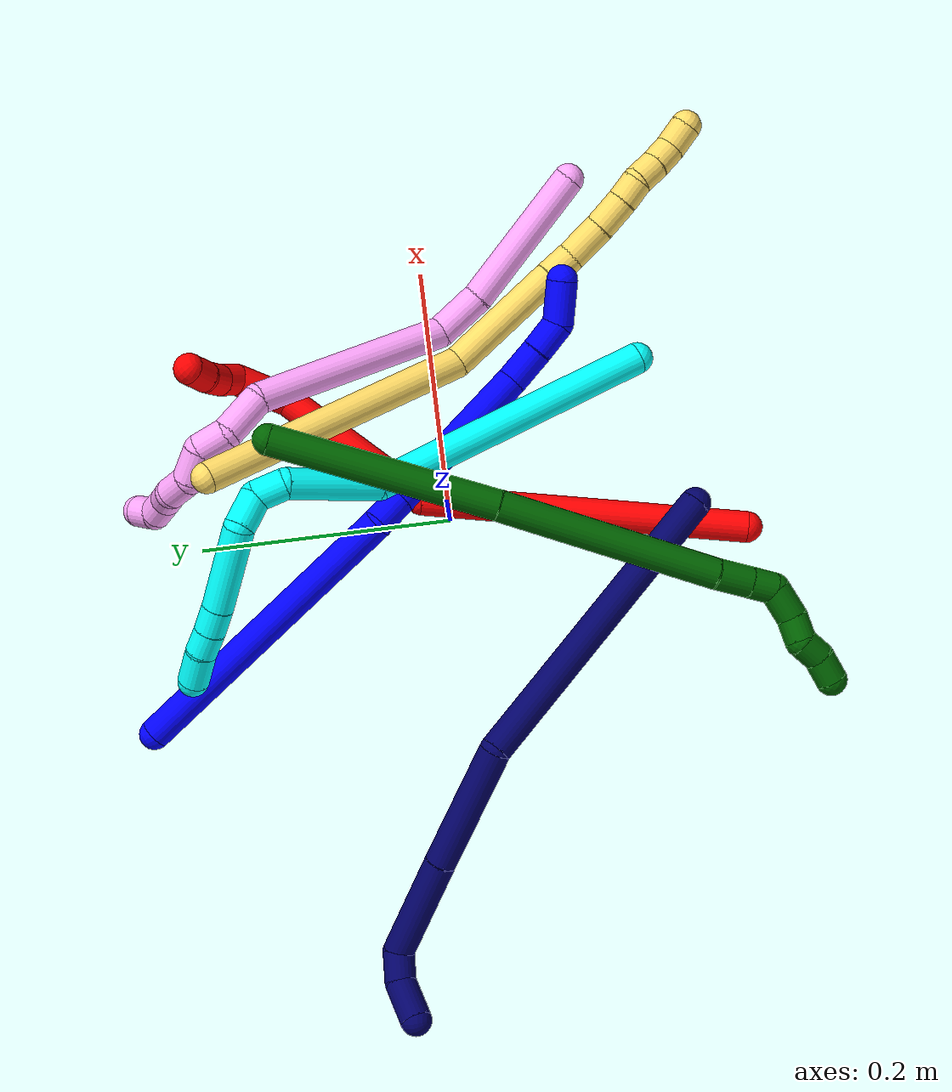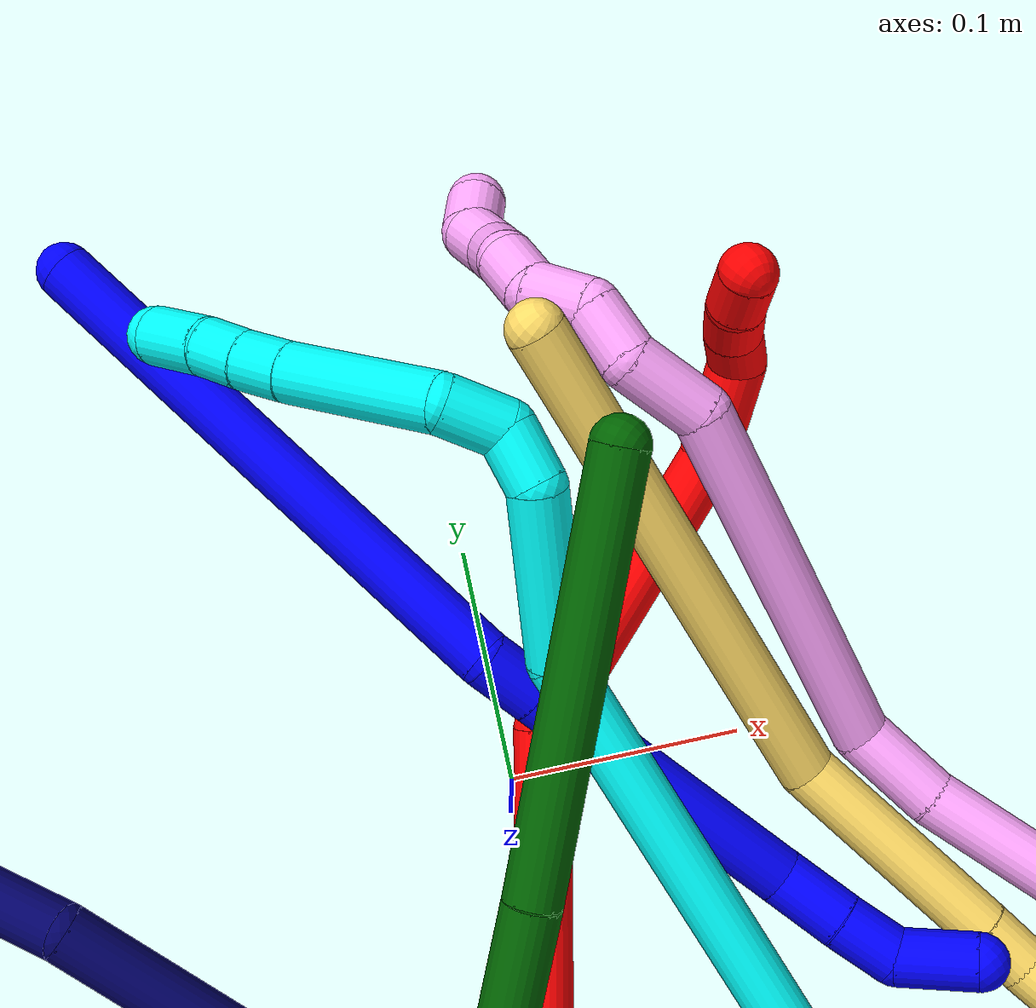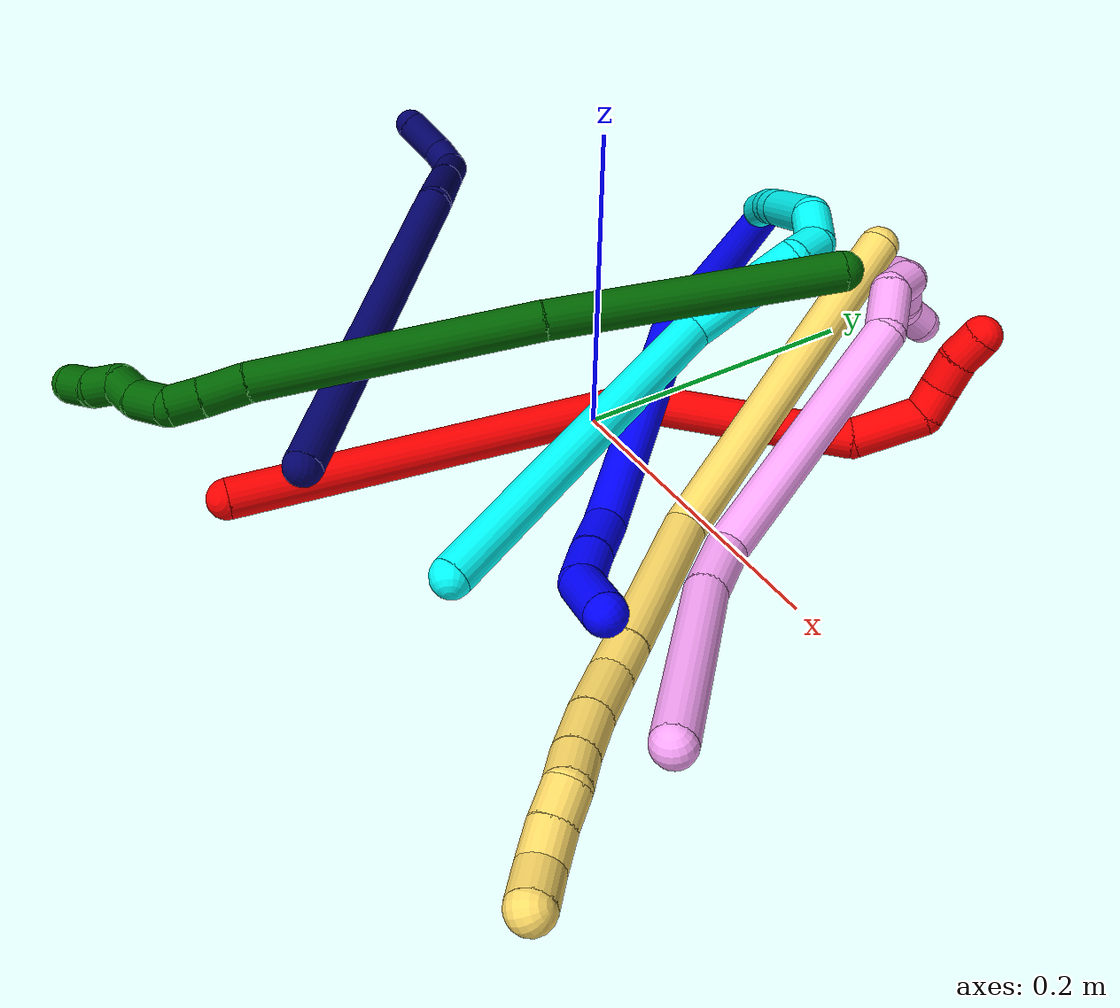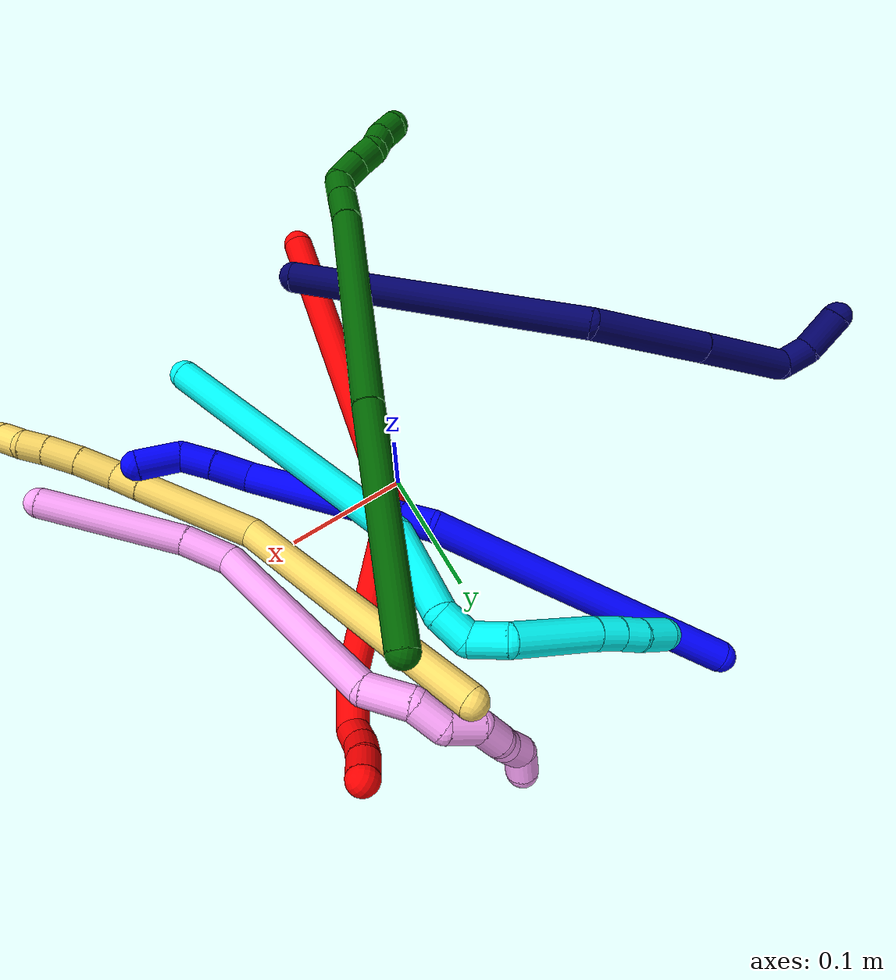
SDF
<sdf version="1.7">
 <world name="default">
  <plugin name="TubeGeneratorPlugin" filename="libtube_generator_plugin.so"/>
  <model name="photoneo_s_sensor">
   <static>1</static>
   <pose>0 0 2 1.57079 1.57079 3.14159</pose>
   <link name="link">
    <inertial><mass>0.1</mass></inertial>
    <sensor name="sensor" type="depth">
     <update_rate>30</update_rate>
     <camera>
      <horizontal_fov>1.22</horizontal_fov>
      <image><width>1920</width><height>1200</height><format>B8G8R8</format></image>
      <clip><near>0.1</near><far>4</far></clip>
      <depth_camera><output>points</output></depth_camera>
     </camera>
     <plugin name="camera_plugin" filename="libgazebo_ros_depth_camera.so">
      <baseline>0.2</baseline>
      <alwaysOn>1</alwaysOn>
      <updateRate>0.0</updateRate>
      <cameraName>camera_ir</cameraName>
      <imageTopicName>/camera/color/image_raw</imageTopicName>
      <cameraInfoTopicName>/camera/color/camera_info</cameraInfoTopicName>
      <depthImageTopicName>/camera/depth/image_raw</depthImageTopicName>
      <depthImageCameraInfoTopicName>/camera/depth/camera_info</depthImageCameraInfoTopicName>
      <pointCloudTopicName>/camera/depth/points</pointCloudTopicName>
      <frameName>fr_optical</frameName>
      <pointCloudCutoff>0.1</pointCloudCutoff>
      <pointCloudCutoffMax>2.0</pointCloudCutoffMax>
      <distortionK1>0</distortionK1>
      <distortionK2>0</distortionK2>
      <distortionK3>0</distortionK3>
      <distortionT1>0</distortionT1>
      <distortionT2>0</distortionT2>
      <CxPrime>0</CxPrime>
      <Cx>0</Cx>
      <Cy>0</Cy>
      <focalLength>0</focalLength>
      <hackBaseline>0</hackBaseline>
     </plugin>
    </sensor>
   </link>
  </model>
  <gravity>0 0 -9.8</gravity>
  <magnetic_field>6e-06 2.3e-05 -4.2e-05</magnetic_field>
  <atmosphere type="adiabatic"/>
  <physics name="default_physics" default="0" type="ode">
   <max_step_size>0.003</max_step_size>
   <real_time_factor>1</real_time_factor>
   <real_time_update_rate>1000</real_time_update_rate>
   <max_contacts>10000</max_contacts>
   <ode>
    <solver>
     <type>quick</type>
     <iters>100</iters>
     <sor>1.3</sor>
     <use_dynamic_moi_rescaling>0</use_dynamic_moi_rescaling>
    </solver>
    <constraints>
     <contact_max_correcting_vel>0</contact_max_correcting_vel>
     <contact_surface_layer>0.001</contact_surface_layer>
     <cfm>0</cfm>
     <erp>0.2</erp>
    </constraints>
   </ode>
  </physics>
  <scene><ambient>0.4 0.4 0.4 1</ambient><background>0.7 0.7 0.7 1</background><shadows>0</shadows></scene>
  <audio><device>default</device></audio>
  <spherical_coordinates>
   <surface_model>EARTH_WGS84</surface_model>
   <latitude_deg>0</latitude_deg>
   <longitude_deg>0</longitude_deg>
   <elevation>0</elevation>
   <heading_deg>0</heading_deg>
  </spherical_coordinates>
  <model name="bin">
   <static>1</static>
   <link name="bottom">
    <collision name="collision-bottom">
     <pose>0 0 -0.01 0 -0 0</pose>
     <geometry><box><size>0.8 0.6 0.02</size></box></geometry>
     <surface>
      <friction><ode><mu>100</mu><mu2>100</mu2></ode></friction>
      <contact><collide_bitmask>65535</collide_bitmask></contact>
     </surface>
    </collision>
   </link>
   <link name="west_wall">
    <collision name="collision-west_wall">
     <pose>-0.41 0 0.1 0 -0 0</pose>
     <geometry><box><size>0.02 0.6 0.2</size></box></geometry>
     <surface>
      <friction><ode><mu>100</mu><mu2>100</mu2></ode></friction>
      <contact><collide_bitmask>65535</collide_bitmask></contact>
     </surface>
    </collision>
   </link>
   <link name="east_wall">
    <collision name="collision-east_wall">
     <pose>0.41 0 0.1 0 -0 0</pose>
     <geometry><box><size>0.02 0.6 0.2</size></box></geometry>
     <surface>
      <friction><ode><mu>100</mu><mu2>100</mu2></ode></friction>
      <contact><collide_bitmask>65535</collide_bitmask></contact>
     </surface>
    </collision>
   </link>
   <link name="south_wall">
    <collision name="collision-south_wall">
     <pose>0 -0.31 0.1 0 -0 0</pose>
     <geometry><box><size>0.8 0.02 0.2</size></box></geometry>
     <surface>
      <friction><ode><mu>100</mu><mu2>100</mu2></ode></friction>
      <contact><collide_bitmask>65535</collide_bitmask></contact>
     </surface>
    </collision>
   </link>
   <link name="north_wall">
    <collision name="collision-north_wall">
     <pose>0 0.31 0.1 0 -0 0</pose>
     <geometry><box><size>0.8 0.02 0.2</size></box></geometry>
     <surface>
      <friction><ode><mu>100</mu><mu2>100</mu2></ode></friction>
      <contact><collide_bitmask>65535</collide_bitmask></contact>
     </surface>
    </collision>
   </link>
  </model>
  <model name="1">
   <static>0</static>
   <link name="1">
    <collision name="collision-cylinder-e_1_1_4">
     <pose>-0.00286 -0.023312 -0.120487 2.95047 -0.0233 -0.241902</pose>
     <geometry><cylinder><radius>0.0125</radius><length>0.24551</length></cylinder></geometry>
     <surface>
      <friction><ode><mu>1.16</mu><mu2>1.16</mu2><slip1>0</slip1><slip2>0</slip2></ode></friction>
      <contact><ode><kp>1e+06</kp><kd>1</kd><max_vel>0</max_vel><min_depth>0.001</min_depth></ode></contact>
     </surface>
    </collision>
    <visual name="visual-cylinder-e_1_1_4">
     <pose>-0.00286 -0.023312 -0.120487 2.95047 -0.0233 -0.241902</pose>
     <geometry><cylinder><radius>0.0125</radius><length>0.24551</length></cylinder></geometry>
     <material><ambient>0 0 1 1</ambient></material>
    </visual>
    <collision name="collision-cylinder-e_2_4_5">
     <pose>-0.001154 -0.048313 -0.253252 3.00494 0.352973 2.40883</pose>
     <geometry><cylinder><radius>0.0125</radius><length>0.026415</length></cylinder></geometry>
     <surface>
      <friction><ode><mu>1.16</mu><mu2>1.16</mu2><slip1>0</slip1><slip2>0</slip2></ode></friction>
      <contact><ode><kp>1e+06</kp><kd>1</kd><max_vel>0</max_vel><min_depth>0.001</min_depth></ode></contact>
     </surface>
    </collision>
    <visual name="visual-cylinder-e_2_4_5">
     <pose>-0.001154 -0.048313 -0.253252 3.00494 0.352973 2.40883</pose>
     <geometry><cylinder><radius>0.0125</radius><length>0.026415</length></cylinder></geometry>
     <material><ambient>0 0 1 1</ambient></material>
    </visual>
    <collision name="collision-cylinder-e_3_5_6">
     <pose>0.026538 -0.058547 -0.328056 3.00576 0.351263 2.40954</pose>
     <geometry><cylinder><radius>0.0125</radius><length>0.134424</length></cylinder></geometry>
     <surface>
      <friction><ode><mu>1.16</mu><mu2>1.16</mu2><slip1>0</slip1><slip2>0</slip2></ode></friction>
      <contact><ode><kp>1e+06</kp><kd>1</kd><max_vel>0</max_vel><min_depth>0.001</min_depth></ode></contact>
     </surface>
    </collision>
    <visual name="visual-cylinder-e_3_5_6">
     <pose>0.026538 -0.058547 -0.328056 3.00576 0.351263 2.40954</pose>
     <geometry><cylinder><radius>0.0125</radius><length>0.134424</length></cylinder></geometry>
     <material><ambient>0 0 1 1</ambient></material>
    </visual>
    <collision name="collision-cylinder-e_4_6_7">
     <pose>0.049884 -0.071721 -0.405753 2.84544 0.01382 0.092578</pose>
     <geometry><cylinder><radius>0.0125</radius><length>0.031725</length></cylinder></geometry>
     <surface>
      <friction><ode><mu>1.16</mu><mu2>1.16</mu2><slip1>0</slip1><slip2>0</slip2></ode></friction>
      <contact><ode><kp>1e+06</kp><kd>1</kd><max_vel>0</max_vel><min_depth>0.001</min_depth></ode></contact>
     </surface>
    </collision>
    <visual name="visual-cylinder-e_4_6_7">
     <pose>0.049884 -0.071721 -0.405753 2.84544 0.01382 0.092578</pose>
     <geometry><cylinder><radius>0.0125</radius><length>0.031725</length></cylinder></geometry>
     <material><ambient>0 0 1 1</ambient></material>
    </visual>
    <collision name="collision-cylinder-e_5_7_8">
     <pose>0.051203 -0.080473 -0.433659 2.82853 0.082016 0.508697</pose>
     <geometry><cylinder><radius>0.0125</radius><length>0.026863</length></cylinder></geometry>
     <surface>
      <friction><ode><mu>1.16</mu><mu2>1.16</mu2><slip1>0</slip1><slip2>0</slip2></ode></friction>
      <contact><ode><kp>1e+06</kp><kd>1</kd><max_vel>0</max_vel><min_depth>0.001</min_depth></ode></contact>
     </surface>
    </collision>
    <visual name="visual-cylinder-e_5_7_8">
     <pose>0.051203 -0.080473 -0.433659 2.82853 0.082016 0.508697</pose>
     <geometry><cylinder><radius>0.0125</radius><length>0.026863</length></cylinder></geometry>
     <material><ambient>0 0 1 1</ambient></material>
    </visual>
    <collision name="collision-cylinder-e_6_8_2">
     <pose>0.0537 -0.098366 -0.457156 2.23415 0.079736 0.163231</pose>
     <geometry><cylinder><radius>0.0125</radius><length>0.035064</length></cylinder></geometry>
     <surface>
      <friction><ode><mu>1.16</mu><mu2>1.16</mu2><slip1>0</slip1><slip2>0</slip2></ode></friction>
      <contact><ode><kp>1e+06</kp><kd>1</kd><max_vel>0</max_vel><min_depth>0.001</min_depth></ode></contact>
     </surface>
    </collision>
    <visual name="visual-cylinder-e_6_8_2">
     <pose>0.0537 -0.098366 -0.457156 2.23415 0.079736 0.163231</pose>
     <geometry><cylinder><radius>0.0125</radius><length>0.035064</length></cylinder></geometry>
     <material><ambient>0 0 1 1</ambient></material>
    </visual>
    <collision name="collision-sphere-2">
     <pose>0.055097 -0.112136 -0.467917 0 -0 0</pose>
     <geometry><sphere><radius>0.0125</radius></sphere></geometry>
     <surface>
      <friction><ode><mu>1.16</mu><mu2>1.16</mu2><slip1>0</slip1><slip2>0</slip2></ode></friction>
      <contact><ode><kp>1e+06</kp><kd>1</kd><max_vel>0</max_vel><min_depth>0.001</min_depth></ode></contact>
     </surface>
    </collision>
    <visual name="visual-sphere-2">
     <pose>0.055097 -0.112136 -0.467917 0 -0 0</pose>
     <geometry><sphere><radius>0.0125</radius></sphere></geometry>
     <material><ambient>0 0 1 1</ambient></material>
    </visual>
    <collision name="collision-sphere-4">
     <pose>-0.00572 -0.046624 -0.240975 0 -0 0</pose>
     <geometry><sphere><radius>0.0125</radius></sphere></geometry>
     <surface>
      <friction><ode><mu>1.16</mu><mu2>1.16</mu2><slip1>0</slip1><slip2>0</slip2></ode></friction>
      <contact><ode><kp>1e+06</kp><kd>1</kd><max_vel>0</max_vel><min_depth>0.001</min_depth></ode></contact>
     </surface>
    </collision>
    <visual name="visual-sphere-4">
     <pose>-0.00572 -0.046624 -0.240975 0 -0 0</pose>
     <geometry><sphere><radius>0.0125</radius></sphere></geometry>
     <material><ambient>0 0 1 1</ambient></material>
    </visual>
    <collision name="collision-sphere-1">
     <geometry><sphere><radius>0.0125</radius></sphere></geometry>
     <surface>
      <friction><ode><mu>1.16</mu><mu2>1.16</mu2><slip1>0</slip1><slip2>0</slip2></ode></friction>
      <contact><ode><kp>1e+06</kp><kd>1</kd><max_vel>0</max_vel><min_depth>0.001</min_depth></ode></contact>
     </surface>
    </collision>
    <visual name="visual-sphere-1">
     <geometry><sphere><radius>0.0125</radius></sphere></geometry>
     <material><ambient>0 0 1 1</ambient></material>
    </visual>
    <collision name="collision-sphere-8">
     <pose>0.052304 -0.084596 -0.446395 0 -0 0</pose>
     <geometry><sphere><radius>0.0125</radius></sphere></geometry>
     <surface>
      <friction><ode><mu>1.16</mu><mu2>1.16</mu2><slip1>0</slip1><slip2>0</slip2></ode></friction>
      <contact><ode><kp>1e+06</kp><kd>1</kd><max_vel>0</max_vel><min_depth>0.001</min_depth></ode></contact>
     </surface>
    </collision>
    <visual name="visual-sphere-8">
     <pose>0.052304 -0.084596 -0.446395 0 -0 0</pose>
     <geometry><sphere><radius>0.0125</radius></sphere></geometry>
     <material><ambient>0 0 1 1</ambient></material>
    </visual>
    <collision name="collision-sphere-5">
     <pose>0.003411 -0.050001 -0.26553 0 -0 0</pose>
     <geometry><sphere><radius>0.0125</radius></sphere></geometry>
     <surface>
      <friction><ode><mu>1.16</mu><mu2>1.16</mu2><slip1>0</slip1><slip2>0</slip2></ode></friction>
      <contact><ode><kp>1e+06</kp><kd>1</kd><max_vel>0</max_vel><min_depth>0.001</min_depth></ode></contact>
     </surface>
    </collision>
    <visual name="visual-sphere-5">
     <pose>0.003411 -0.050001 -0.26553 0 -0 0</pose>
     <geometry><sphere><radius>0.0125</radius></sphere></geometry>
     <material><ambient>0 0 1 1</ambient></material>
    </visual>
    <collision name="collision-sphere-6">
     <pose>0.049665 -0.067092 -0.390583 0 -0 0</pose>
     <geometry><sphere><radius>0.0125</radius></sphere></geometry>
     <surface>
      <friction><ode><mu>1.16</mu><mu2>1.16</mu2><slip1>0</slip1><slip2>0</slip2></ode></friction>
      <contact><ode><kp>1e+06</kp><kd>1</kd><max_vel>0</max_vel><min_depth>0.001</min_depth></ode></contact>
     </surface>
    </collision>
    <visual name="visual-sphere-6">
     <pose>0.049665 -0.067092 -0.390583 0 -0 0</pose>
     <geometry><sphere><radius>0.0125</radius></sphere></geometry>
     <material><ambient>0 0 1 1</ambient></material>
    </visual>
    <collision name="collision-sphere-7">
     <pose>0.050103 -0.07635 -0.420924 0 -0 0</pose>
     <geometry><sphere><radius>0.0125</radius></sphere></geometry>
     <surface>
      <friction><ode><mu>1.16</mu><mu2>1.16</mu2><slip1>0</slip1><slip2>0</slip2></ode></friction>
      <contact><ode><kp>1e+06</kp><kd>1</kd><max_vel>0</max_vel><min_depth>0.001</min_depth></ode></contact>
     </surface>
    </collision>
    <visual name="visual-sphere-7">
     <pose>0.050103 -0.07635 -0.420924 0 -0 0</pose>
     <geometry><sphere><radius>0.0125</radius></sphere></geometry>
     <material><ambient>0 0 1 1</ambient></material>
    </visual>
    <inertial>
     <pose>0.015351 -0.045511 -0.241841 0 -0 0</pose>
     <mass>0.5</mass>
     <inertia>
      <ixx>0.000912</ixx>
      <ixy>0</ixy>
      <ixz>0</ixz>
      <iyy>-0.001203</iyy>
      <iyz>0</iyz>
      <izz>0.000188</izz>
     </inertia>
    </inertial>
   </link>
   <pose>-0.140643 0.253968 0.012121 -1.73472 1.17436 0.302519</pose>
  </model>
  <model name="2">
   <static>0</static>
   <link name="2">
    <collision name="collision-cylinder-e_1_1_4">
     <pose>0.046557 0.091981 -0.079503 -2.28356 0.365711 -0.768346</pose>
     <geometry><cylinder><radius>0.0125</radius><length>0.260375</length></cylinder></geometry>
     <surface>
      <friction><ode><mu>1.16</mu><mu2>1.16</mu2><slip1>0</slip1><slip2>0</slip2></ode></friction>
      <contact><ode><kp>1e+06</kp><kd>1</kd><max_vel>0</max_vel><min_depth>0.001</min_depth></ode></contact>
     </surface>
    </collision>
    <visual name="visual-cylinder-e_1_1_4">
     <pose>0.046557 0.091981 -0.079503 -2.28356 0.365711 -0.768346</pose>
     <geometry><cylinder><radius>0.0125</radius><length>0.260375</length></cylinder></geometry>
     <material><ambient>1 0 0 1</ambient></material>
    </visual>
    <collision name="collision-cylinder-e_2_4_5">
     <pose>0.145352 0.222089 -0.177426 -2.02083 0.889639 -1.29933</pose>
     <geometry><cylinder><radius>0.0125</radius><length>0.134488</length></cylinder></geometry>
     <surface>
      <friction><ode><mu>1.16</mu><mu2>1.16</mu2><slip1>0</slip1><slip2>0</slip2></ode></friction>
      <contact><ode><kp>1e+06</kp><kd>1</kd><max_vel>0</max_vel><min_depth>0.001</min_depth></ode></contact>
     </surface>
    </collision>
    <visual name="visual-cylinder-e_2_4_5">
     <pose>0.145352 0.222089 -0.177426 -2.02083 0.889639 -1.29933</pose>
     <geometry><cylinder><radius>0.0125</radius><length>0.134488</length></cylinder></geometry>
     <material><ambient>1 0 0 1</ambient></material>
    </visual>
    <collision name="collision-cylinder-e_3_5_6">
     <pose>0.206717 0.280123 -0.200879 -1.81849 0.418287 -0.532276</pose>
     <geometry><cylinder><radius>0.0125</radius><length>0.044941</length></cylinder></geometry>
     <surface>
      <friction><ode><mu>1.16</mu><mu2>1.16</mu2><slip1>0</slip1><slip2>0</slip2></ode></friction>
      <contact><ode><kp>1e+06</kp><kd>1</kd><max_vel>0</max_vel><min_depth>0.001</min_depth></ode></contact>
     </surface>
    </collision>
    <visual name="visual-cylinder-e_3_5_6">
     <pose>0.206717 0.280123 -0.200879 -1.81849 0.418287 -0.532276</pose>
     <geometry><cylinder><radius>0.0125</radius><length>0.044941</length></cylinder></geometry>
     <material><ambient>1 0 0 1</ambient></material>
    </visual>
    <collision name="collision-cylinder-e_4_6_7">
     <pose>0.213217 0.309679 -0.205785 -1.55754 -0.265821 0.26236</pose>
     <geometry><cylinder><radius>0.0125</radius><length>0.020005</length></cylinder></geometry>
     <surface>
      <friction><ode><mu>1.16</mu><mu2>1.16</mu2><slip1>0</slip1><slip2>0</slip2></ode></friction>
      <contact><ode><kp>1e+06</kp><kd>1</kd><max_vel>0</max_vel><min_depth>0.001</min_depth></ode></contact>
     </surface>
    </collision>
    <visual name="visual-cylinder-e_4_6_7">
     <pose>0.213217 0.309679 -0.205785 -1.55754 -0.265821 0.26236</pose>
     <geometry><cylinder><radius>0.0125</radius><length>0.020005</length></cylinder></geometry>
     <material><ambient>1 0 0 1</ambient></material>
    </visual>
    <collision name="collision-cylinder-e_5_7_8">
     <pose>0.208462 0.328938 -0.203554 -1.35532 -0.213031 0.171675</pose>
     <geometry><cylinder><radius>0.0125</radius><length>0.020126</length></cylinder></geometry>
     <surface>
      <friction><ode><mu>1.16</mu><mu2>1.16</mu2><slip1>0</slip1><slip2>0</slip2></ode></friction>
      <contact><ode><kp>1e+06</kp><kd>1</kd><max_vel>0</max_vel><min_depth>0.001</min_depth></ode></contact>
     </surface>
    </collision>
    <visual name="visual-cylinder-e_5_7_8">
     <pose>0.208462 0.328938 -0.203554 -1.35532 -0.213031 0.171675</pose>
     <geometry><cylinder><radius>0.0125</radius><length>0.020126</length></cylinder></geometry>
     <material><ambient>1 0 0 1</ambient></material>
    </visual>
    <collision name="collision-cylinder-e_6_8_2">
     <pose>0.206489 0.348387 -0.199509 -1.37597 0.015394 -0.012653</pose>
     <geometry><cylinder><radius>0.0125</radius><length>0.020065</length></cylinder></geometry>
     <surface>
      <friction><ode><mu>1.16</mu><mu2>1.16</mu2><slip1>0</slip1><slip2>0</slip2></ode></friction>
      <contact><ode><kp>1e+06</kp><kd>1</kd><max_vel>0</max_vel><min_depth>0.001</min_depth></ode></contact>
     </surface>
    </collision>
    <visual name="visual-cylinder-e_6_8_2">
     <pose>0.206489 0.348387 -0.199509 -1.37597 0.015394 -0.012653</pose>
     <geometry><cylinder><radius>0.0125</radius><length>0.020065</length></cylinder></geometry>
     <material><ambient>1 0 0 1</ambient></material>
    </visual>
    <collision name="collision-sphere-2">
     <pose>0.206643 0.358229 -0.197567 0 -0 0</pose>
     <geometry><sphere><radius>0.0125</radius></sphere></geometry>
     <surface>
      <friction><ode><mu>1.16</mu><mu2>1.16</mu2><slip1>0</slip1><slip2>0</slip2></ode></friction>
      <contact><ode><kp>1e+06</kp><kd>1</kd><max_vel>0</max_vel><min_depth>0.001</min_depth></ode></contact>
     </surface>
    </collision>
    <visual name="visual-sphere-2">
     <pose>0.206643 0.358229 -0.197567 0 -0 0</pose>
     <geometry><sphere><radius>0.0125</radius></sphere></geometry>
     <material><ambient>1 0 0 1</ambient></material>
    </visual>
    <collision name="collision-sphere-4">
     <pose>0.093114 0.183962 -0.159007 0 -0 0</pose>
     <geometry><sphere><radius>0.0125</radius></sphere></geometry>
     <surface>
      <friction><ode><mu>1.16</mu><mu2>1.16</mu2><slip1>0</slip1><slip2>0</slip2></ode></friction>
      <contact><ode><kp>1e+06</kp><kd>1</kd><max_vel>0</max_vel><min_depth>0.001</min_depth></ode></contact>
     </surface>
    </collision>
    <visual name="visual-sphere-4">
     <pose>0.093114 0.183962 -0.159007 0 -0 0</pose>
     <geometry><sphere><radius>0.0125</radius></sphere></geometry>
     <material><ambient>1 0 0 1</ambient></material>
    </visual>
    <collision name="collision-sphere-1">
     <geometry><sphere><radius>0.0125</radius></sphere></geometry>
     <surface>
      <friction><ode><mu>1.16</mu><mu2>1.16</mu2><slip1>0</slip1><slip2>0</slip2></ode></friction>
      <contact><ode><kp>1e+06</kp><kd>1</kd><max_vel>0</max_vel><min_depth>0.001</min_depth></ode></contact>
     </surface>
    </collision>
    <visual name="visual-sphere-1">
     <geometry><sphere><radius>0.0125</radius></sphere></geometry>
     <material><ambient>1 0 0 1</ambient></material>
    </visual>
    <collision name="collision-sphere-8">
     <pose>0.206334 0.338546 -0.201451 0 -0 0</pose>
     <geometry><sphere><radius>0.0125</radius></sphere></geometry>
     <surface>
      <friction><ode><mu>1.16</mu><mu2>1.16</mu2><slip1>0</slip1><slip2>0</slip2></ode></friction>
      <contact><ode><kp>1e+06</kp><kd>1</kd><max_vel>0</max_vel><min_depth>0.001</min_depth></ode></contact>
     </surface>
    </collision>
    <visual name="visual-sphere-8">
     <pose>0.206334 0.338546 -0.201451 0 -0 0</pose>
     <geometry><sphere><radius>0.0125</radius></sphere></geometry>
     <material><ambient>1 0 0 1</ambient></material>
    </visual>
    <collision name="collision-sphere-5">
     <pose>0.19759 0.260216 -0.195845 0 -0 0</pose>
     <geometry><sphere><radius>0.0125</radius></sphere></geometry>
     <surface>
      <friction><ode><mu>1.16</mu><mu2>1.16</mu2><slip1>0</slip1><slip2>0</slip2></ode></friction>
      <contact><ode><kp>1e+06</kp><kd>1</kd><max_vel>0</max_vel><min_depth>0.001</min_depth></ode></contact>
     </surface>
    </collision>
    <visual name="visual-sphere-5">
     <pose>0.19759 0.260216 -0.195845 0 -0 0</pose>
     <geometry><sphere><radius>0.0125</radius></sphere></geometry>
     <material><ambient>1 0 0 1</ambient></material>
    </visual>
    <collision name="collision-sphere-6">
     <pose>0.215845 0.300029 -0.205913 0 -0 0</pose>
     <geometry><sphere><radius>0.0125</radius></sphere></geometry>
     <surface>
      <friction><ode><mu>1.16</mu><mu2>1.16</mu2><slip1>0</slip1><slip2>0</slip2></ode></friction>
      <contact><ode><kp>1e+06</kp><kd>1</kd><max_vel>0</max_vel><min_depth>0.001</min_depth></ode></contact>
     </surface>
    </collision>
    <visual name="visual-sphere-6">
     <pose>0.215845 0.300029 -0.205913 0 -0 0</pose>
     <geometry><sphere><radius>0.0125</radius></sphere></geometry>
     <material><ambient>1 0 0 1</ambient></material>
    </visual>
    <collision name="collision-sphere-7">
     <pose>0.210589 0.31933 -0.205657 0 -0 0</pose>
     <geometry><sphere><radius>0.0125</radius></sphere></geometry>
     <surface>
      <friction><ode><mu>1.16</mu><mu2>1.16</mu2><slip1>0</slip1><slip2>0</slip2></ode></friction>
      <contact><ode><kp>1e+06</kp><kd>1</kd><max_vel>0</max_vel><min_depth>0.001</min_depth></ode></contact>
     </surface>
    </collision>
    <visual name="visual-sphere-7">
     <pose>0.210589 0.31933 -0.205657 0 -0 0</pose>
     <geometry><sphere><radius>0.0125</radius></sphere></geometry>
     <material><ambient>1 0 0 1</ambient></material>
    </visual>
    <inertial>
     <pose>0.107129 0.172425 -0.131613 0 -0 0</pose>
     <mass>0.5</mass>
     <inertia>
      <ixx>-3.4e-05</ixx>
      <ixy>0</ixy>
      <ixz>0</ixz>
      <iyy>-0.001365</iyy>
      <iyz>0</iyz>
      <izz>-0.001887</izz>
     </inertia>
    </inertial>
   </link>
   <pose>-0.035132 -0.234064 0.011494 0.907414 0.403834 0.205644</pose>
  </model>
  <model name="3">
   <static>0</static>
   <link name="3">
    <collision name="collision-cylinder-e_1_1_4">
     <pose>0.023917 0.066223 0.091809 -0.624882 0.208216 -0.067477</pose>
     <geometry><cylinder><radius>0.0125</radius><length>0.231399</length></cylinder></geometry>
     <surface>
      <friction><ode><mu>1.16</mu><mu2>1.16</mu2><slip1>0</slip1><slip2>0</slip2></ode></friction>
      <contact><ode><kp>1e+06</kp><kd>1</kd><max_vel>0</max_vel><min_depth>0.001</min_depth></ode></contact>
     </surface>
    </collision>
    <visual name="visual-cylinder-e_1_1_4">
     <pose>0.023917 0.066223 0.091809 -0.624882 0.208216 -0.067477</pose>
     <geometry><cylinder><radius>0.0125</radius><length>0.231399</length></cylinder></geometry>
     <material><ambient>0.003922 1 0.996078 1</ambient></material>
    </visual>
    <collision name="collision-cylinder-e_2_4_5">
     <pose>0.071957 0.155408 0.203581 -0.85519 0.670352 -0.31484</pose>
     <geometry><cylinder><radius>0.0125</radius><length>0.077659</length></cylinder></geometry>
     <surface>
      <friction><ode><mu>1.16</mu><mu2>1.16</mu2><slip1>0</slip1><slip2>0</slip2></ode></friction>
      <contact><ode><kp>1e+06</kp><kd>1</kd><max_vel>0</max_vel><min_depth>0.001</min_depth></ode></contact>
     </surface>
    </collision>
    <visual name="visual-cylinder-e_2_4_5">
     <pose>0.071957 0.155408 0.203581 -0.85519 0.670352 -0.31484</pose>
     <geometry><cylinder><radius>0.0125</radius><length>0.077659</length></cylinder></geometry>
     <material><ambient>0.003922 1 0.996078 1</ambient></material>
    </visual>
    <collision name="collision-cylinder-e_3_5_6">
     <pose>0.097144 0.18712 0.232317 -0.783979 0.085647 -0.035423</pose>
     <geometry><cylinder><radius>0.0125</radius><length>0.024872</length></cylinder></geometry>
     <surface>
      <friction><ode><mu>1.16</mu><mu2>1.16</mu2><slip1>0</slip1><slip2>0</slip2></ode></friction>
      <contact><ode><kp>1e+06</kp><kd>1</kd><max_vel>0</max_vel><min_depth>0.001</min_depth></ode></contact>
     </surface>
    </collision>
    <visual name="visual-cylinder-e_3_5_6">
     <pose>0.097144 0.18712 0.232317 -0.783979 0.085647 -0.035423</pose>
     <geometry><cylinder><radius>0.0125</radius><length>0.024872</length></cylinder></geometry>
     <material><ambient>0.003922 1 0.996078 1</ambient></material>
    </visual>
    <collision name="collision-cylinder-e_4_6_7">
     <pose>0.096903 0.196833 0.25472 -0.070551 -0.095242 0.003364</pose>
     <geometry><cylinder><radius>0.0125</radius><length>0.02745</length></cylinder></geometry>
     <surface>
      <friction><ode><mu>1.16</mu><mu2>1.16</mu2><slip1>0</slip1><slip2>0</slip2></ode></friction>
      <contact><ode><kp>1e+06</kp><kd>1</kd><max_vel>0</max_vel><min_depth>0.001</min_depth></ode></contact>
     </surface>
    </collision>
    <visual name="visual-cylinder-e_4_6_7">
     <pose>0.096903 0.196833 0.25472 -0.070551 -0.095242 0.003364</pose>
     <geometry><cylinder><radius>0.0125</radius><length>0.02745</length></cylinder></geometry>
     <material><ambient>0.003922 1 0.996078 1</ambient></material>
    </visual>
    <collision name="collision-cylinder-e_5_7_8">
     <pose>0.073261 0.204582 0.293759 -0.260968 -0.704068 0.096336</pose>
     <geometry><cylinder><radius>0.0125</radius><length>0.069011</length></cylinder></geometry>
     <surface>
      <friction><ode><mu>1.16</mu><mu2>1.16</mu2><slip1>0</slip1><slip2>0</slip2></ode></friction>
      <contact><ode><kp>1e+06</kp><kd>1</kd><max_vel>0</max_vel><min_depth>0.001</min_depth></ode></contact>
     </surface>
    </collision>
    <visual name="visual-cylinder-e_5_7_8">
     <pose>0.073261 0.204582 0.293759 -0.260968 -0.704068 0.096336</pose>
     <geometry><cylinder><radius>0.0125</radius><length>0.069011</length></cylinder></geometry>
     <material><ambient>0.003922 1 0.996078 1</ambient></material>
    </visual>
    <collision name="collision-cylinder-e_6_8_9">
     <pose>0.044208 0.214103 0.326886 -0.340615 -0.687035 0.122875</pose>
     <geometry><cylinder><radius>0.0125</radius><length>0.021181</length></cylinder></geometry>
     <surface>
      <friction><ode><mu>1.16</mu><mu2>1.16</mu2><slip1>0</slip1><slip2>0</slip2></ode></friction>
      <contact><ode><kp>1e+06</kp><kd>1</kd><max_vel>0</max_vel><min_depth>0.001</min_depth></ode></contact>
     </surface>
    </collision>
    <visual name="visual-cylinder-e_6_8_9">
     <pose>0.044208 0.214103 0.326886 -0.340615 -0.687035 0.122875</pose>
     <geometry><cylinder><radius>0.0125</radius><length>0.021181</length></cylinder></geometry>
     <material><ambient>0.003922 1 0.996078 1</ambient></material>
    </visual>
    <collision name="collision-cylinder-e_7_9_10">
     <pose>0.031207 0.220047 0.34185 -0.416887 -0.670414 0.147098</pose>
     <geometry><cylinder><radius>0.0125</radius><length>0.020229</length></cylinder></geometry>
     <surface>
      <friction><ode><mu>1.16</mu><mu2>1.16</mu2><slip1>0</slip1><slip2>0</slip2></ode></friction>
      <contact><ode><kp>1e+06</kp><kd>1</kd><max_vel>0</max_vel><min_depth>0.001</min_depth></ode></contact>
     </surface>
    </collision>
    <visual name="visual-cylinder-e_7_9_10">
     <pose>0.031207 0.220047 0.34185 -0.416887 -0.670414 0.147098</pose>
     <geometry><cylinder><radius>0.0125</radius><length>0.020229</length></cylinder></geometry>
     <material><ambient>0.003922 1 0.996078 1</ambient></material>
    </visual>
    <collision name="collision-cylinder-e_8_10_2">
     <pose>0.014531 0.227186 0.357779 -0.424994 -0.828644 0.189202</pose>
     <geometry><cylinder><radius>0.0125</radius><length>0.028198</length></cylinder></geometry>
     <surface>
      <friction><ode><mu>1.16</mu><mu2>1.16</mu2><slip1>0</slip1><slip2>0</slip2></ode></friction>
      <contact><ode><kp>1e+06</kp><kd>1</kd><max_vel>0</max_vel><min_depth>0.001</min_depth></ode></contact>
     </surface>
    </collision>
    <visual name="visual-cylinder-e_8_10_2">
     <pose>0.014531 0.227186 0.357779 -0.424994 -0.828644 0.189202</pose>
     <geometry><cylinder><radius>0.0125</radius><length>0.028198</length></cylinder></geometry>
     <material><ambient>0.003922 1 0.996078 1</ambient></material>
    </visual>
    <collision name="collision-sphere-2">
     <pose>0.00414 0.231115 0.36646 0 -0 0</pose>
     <geometry><sphere><radius>0.0125</radius></sphere></geometry>
     <surface>
      <friction><ode><mu>1.16</mu><mu2>1.16</mu2><slip1>0</slip1><slip2>0</slip2></ode></friction>
      <contact><ode><kp>1e+06</kp><kd>1</kd><max_vel>0</max_vel><min_depth>0.001</min_depth></ode></contact>
     </surface>
    </collision>
    <visual name="visual-sphere-2">
     <pose>0.00414 0.231115 0.36646 0 -0 0</pose>
     <geometry><sphere><radius>0.0125</radius></sphere></geometry>
     <material><ambient>0.003922 1 0.996078 1</ambient></material>
    </visual>
    <collision name="collision-sphere-10">
     <pose>0.024922 0.223256 0.349097 0 -0 0</pose>
     <geometry><sphere><radius>0.0125</radius></sphere></geometry>
     <surface>
      <friction><ode><mu>1.16</mu><mu2>1.16</mu2><slip1>0</slip1><slip2>0</slip2></ode></friction>
      <contact><ode><kp>1e+06</kp><kd>1</kd><max_vel>0</max_vel><min_depth>0.001</min_depth></ode></contact>
     </surface>
    </collision>
    <visual name="visual-sphere-10">
     <pose>0.024922 0.223256 0.349097 0 -0 0</pose>
     <geometry><sphere><radius>0.0125</radius></sphere></geometry>
     <material><ambient>0.003922 1 0.996078 1</ambient></material>
    </visual>
    <collision name="collision-sphere-9">
     <pose>0.037491 0.216838 0.334603 0 -0 0</pose>
     <geometry><sphere><radius>0.0125</radius></sphere></geometry>
     <surface>
      <friction><ode><mu>1.16</mu><mu2>1.16</mu2><slip1>0</slip1><slip2>0</slip2></ode></friction>
      <contact><ode><kp>1e+06</kp><kd>1</kd><max_vel>0</max_vel><min_depth>0.001</min_depth></ode></contact>
     </surface>
    </collision>
    <visual name="visual-sphere-9">
     <pose>0.037491 0.216838 0.334603 0 -0 0</pose>
     <geometry><sphere><radius>0.0125</radius></sphere></geometry>
     <material><ambient>0.003922 1 0.996078 1</ambient></material>
    </visual>
    <collision name="collision-sphere-4">
     <pose>0.047834 0.132445 0.183619 0 -0 0</pose>
     <geometry><sphere><radius>0.0125</radius></sphere></geometry>
     <surface>
      <friction><ode><mu>1.16</mu><mu2>1.16</mu2><slip1>0</slip1><slip2>0</slip2></ode></friction>
      <contact><ode><kp>1e+06</kp><kd>1</kd><max_vel>0</max_vel><min_depth>0.001</min_depth></ode></contact>
     </surface>
    </collision>
    <visual name="visual-sphere-4">
     <pose>0.047834 0.132445 0.183619 0 -0 0</pose>
     <geometry><sphere><radius>0.0125</radius></sphere></geometry>
     <material><ambient>0.003922 1 0.996078 1</ambient></material>
    </visual>
    <collision name="collision-sphere-1">
     <geometry><sphere><radius>0.0125</radius></sphere></geometry>
     <surface>
      <friction><ode><mu>1.16</mu><mu2>1.16</mu2><slip1>0</slip1><slip2>0</slip2></ode></friction>
      <contact><ode><kp>1e+06</kp><kd>1</kd><max_vel>0</max_vel><min_depth>0.001</min_depth></ode></contact>
     </surface>
    </collision>
    <visual name="visual-sphere-1">
     <geometry><sphere><radius>0.0125</radius></sphere></geometry>
     <material><ambient>0.003922 1 0.996078 1</ambient></material>
    </visual>
    <collision name="collision-sphere-8">
     <pose>0.050925 0.211368 0.319169 0 -0 0</pose>
     <geometry><sphere><radius>0.0125</radius></sphere></geometry>
     <surface>
      <friction><ode><mu>1.16</mu><mu2>1.16</mu2><slip1>0</slip1><slip2>0</slip2></ode></friction>
      <contact><ode><kp>1e+06</kp><kd>1</kd><max_vel>0</max_vel><min_depth>0.001</min_depth></ode></contact>
     </surface>
    </collision>
    <visual name="visual-sphere-8">
     <pose>0.050925 0.211368 0.319169 0 -0 0</pose>
     <geometry><sphere><radius>0.0125</radius></sphere></geometry>
     <material><ambient>0.003922 1 0.996078 1</ambient></material>
    </visual>
    <collision name="collision-sphere-5">
     <pose>0.09608 0.178371 0.223543 0 -0 0</pose>
     <geometry><sphere><radius>0.0125</radius></sphere></geometry>
     <surface>
      <friction><ode><mu>1.16</mu><mu2>1.16</mu2><slip1>0</slip1><slip2>0</slip2></ode></friction>
      <contact><ode><kp>1e+06</kp><kd>1</kd><max_vel>0</max_vel><min_depth>0.001</min_depth></ode></contact>
     </surface>
    </collision>
    <visual name="visual-sphere-5">
     <pose>0.09608 0.178371 0.223543 0 -0 0</pose>
     <geometry><sphere><radius>0.0125</radius></sphere></geometry>
     <material><ambient>0.003922 1 0.996078 1</ambient></material>
    </visual>
    <collision name="collision-sphere-6">
     <pose>0.098208 0.195869 0.241091 0 -0 0</pose>
     <geometry><sphere><radius>0.0125</radius></sphere></geometry>
     <surface>
      <friction><ode><mu>1.16</mu><mu2>1.16</mu2><slip1>0</slip1><slip2>0</slip2></ode></friction>
      <contact><ode><kp>1e+06</kp><kd>1</kd><max_vel>0</max_vel><min_depth>0.001</min_depth></ode></contact>
     </surface>
    </collision>
    <visual name="visual-sphere-6">
     <pose>0.098208 0.195869 0.241091 0 -0 0</pose>
     <geometry><sphere><radius>0.0125</radius></sphere></geometry>
     <material><ambient>0.003922 1 0.996078 1</ambient></material>
    </visual>
    <collision name="collision-sphere-7">
     <pose>0.095598 0.197796 0.268349 0 -0 0</pose>
     <geometry><sphere><radius>0.0125</radius></sphere></geometry>
     <surface>
      <friction><ode><mu>1.16</mu><mu2>1.16</mu2><slip1>0</slip1><slip2>0</slip2></ode></friction>
      <contact><ode><kp>1e+06</kp><kd>1</kd><max_vel>0</max_vel><min_depth>0.001</min_depth></ode></contact>
     </surface>
    </collision>
    <visual name="visual-sphere-7">
     <pose>0.095598 0.197796 0.268349 0 -0 0</pose>
     <geometry><sphere><radius>0.0125</radius></sphere></geometry>
     <material><ambient>0.003922 1 0.996078 1</ambient></material>
    </visual>
    <inertial>
     <pose>0.046464 0.133922 0.188051 0 -0 0</pose>
     <mass>0.5</mass>
     <inertia>
      <ixx>0.001005</ixx>
      <ixy>0</ixy>
      <ixz>0</ixz>
      <iyy>0.000865</iyy>
      <iyz>0</iyz>
      <izz>-0.00082</izz>
     </inertia>
    </inertial>
   </link>
   <pose>0.107864 -0.163025 0.029554 -0.961775 -1.01994 0.474908</pose>
  </model>
  <model name="4">
   <static>0</static>
   <link name="4">
    <collision name="collision-cylinder-e_1_1_4">
     <pose>-0.054015 0.023887 -0.006722 -1.84512 -1.14016 1.40479</pose>
     <geometry><cylinder><radius>0.0125</radius><length>0.118885</length></cylinder></geometry>
     <surface>
      <friction><ode><mu>1.16</mu><mu2>1.16</mu2><slip1>0</slip1><slip2>0</slip2></ode></friction>
      <contact><ode><kp>1e+06</kp><kd>1</kd><max_vel>0</max_vel><min_depth>0.001</min_depth></ode></contact>
     </surface>
    </collision>
    <visual name="visual-cylinder-e_1_1_4">
     <pose>-0.054015 0.023887 -0.006722 -1.84512 -1.14016 1.40479</pose>
     <geometry><cylinder><radius>0.0125</radius><length>0.118885</length></cylinder></geometry>
     <material><ambient>1 0.65098 0.996078 1</ambient></material>
    </visual>
    <collision name="collision-cylinder-e_2_4_5">
     <pose>-0.124976 0.059071 -0.015136 -1.71944 -0.977642 1.1063</pose>
     <geometry><cylinder><radius>0.0125</radius><length>0.040872</length></cylinder></geometry>
     <surface>
      <friction><ode><mu>1.16</mu><mu2>1.16</mu2><slip1>0</slip1><slip2>0</slip2></ode></friction>
      <contact><ode><kp>1e+06</kp><kd>1</kd><max_vel>0</max_vel><min_depth>0.001</min_depth></ode></contact>
     </surface>
    </collision>
    <visual name="visual-cylinder-e_2_4_5">
     <pose>-0.124976 0.059071 -0.015136 -1.71944 -0.977642 1.1063</pose>
     <geometry><cylinder><radius>0.0125</radius><length>0.040872</length></cylinder></geometry>
     <material><ambient>1 0.65098 0.996078 1</ambient></material>
    </visual>
    <collision name="collision-cylinder-e_3_5_6">
     <pose>-0.185975 0.136481 0.009953 -1.18592 -0.553255 0.378053</pose>
     <geometry><cylinder><radius>0.0125</radius><length>0.167676</length></cylinder></geometry>
     <surface>
      <friction><ode><mu>1.16</mu><mu2>1.16</mu2><slip1>0</slip1><slip2>0</slip2></ode></friction>
      <contact><ode><kp>1e+06</kp><kd>1</kd><max_vel>0</max_vel><min_depth>0.001</min_depth></ode></contact>
     </surface>
    </collision>
    <visual name="visual-cylinder-e_3_5_6">
     <pose>-0.185975 0.136481 0.009953 -1.18592 -0.553255 0.378053</pose>
     <geometry><cylinder><radius>0.0125</radius><length>0.167676</length></cylinder></geometry>
     <material><ambient>1 0.65098 0.996078 1</ambient></material>
    </visual>
    <collision name="collision-cylinder-e_4_6_7">
     <pose>-0.245867 0.211278 0.040241 -1.18701 -1.03676 0.734721</pose>
     <geometry><cylinder><radius>0.0125</radius><length>0.036801</length></cylinder></geometry>
     <surface>
      <friction><ode><mu>1.16</mu><mu2>1.16</mu2><slip1>0</slip1><slip2>0</slip2></ode></friction>
      <contact><ode><kp>1e+06</kp><kd>1</kd><max_vel>0</max_vel><min_depth>0.001</min_depth></ode></contact>
     </surface>
    </collision>
    <visual name="visual-cylinder-e_4_6_7">
     <pose>-0.245867 0.211278 0.040241 -1.18701 -1.03676 0.734721</pose>
     <geometry><cylinder><radius>0.0125</radius><length>0.036801</length></cylinder></geometry>
     <material><ambient>1 0.65098 0.996078 1</ambient></material>
    </visual>
    <collision name="collision-cylinder-e_5_7_8">
     <pose>-0.27031 0.228743 0.040735 -1.90129 -0.747493 1.0044</pose>
     <geometry><cylinder><radius>0.0125</radius><length>0.025316</length></cylinder></geometry>
     <surface>
      <friction><ode><mu>1.16</mu><mu2>1.16</mu2><slip1>0</slip1><slip2>0</slip2></ode></friction>
      <contact><ode><kp>1e+06</kp><kd>1</kd><max_vel>0</max_vel><min_depth>0.001</min_depth></ode></contact>
     </surface>
    </collision>
    <visual name="visual-cylinder-e_5_7_8">
     <pose>-0.27031 0.228743 0.040735 -1.90129 -0.747493 1.0044</pose>
     <geometry><cylinder><radius>0.0125</radius><length>0.025316</length></cylinder></geometry>
     <material><ambient>1 0.65098 0.996078 1</ambient></material>
    </visual>
    <collision name="collision-cylinder-e_6_8_9">
     <pose>-0.29127 0.239008 0.032432 -2.86815 -1.15235 2.72425</pose>
     <geometry><cylinder><radius>0.0125</radius><length>0.027044</length></cylinder></geometry>
     <surface>
      <friction><ode><mu>1.16</mu><mu2>1.16</mu2><slip1>0</slip1><slip2>0</slip2></ode></friction>
      <contact><ode><kp>1e+06</kp><kd>1</kd><max_vel>0</max_vel><min_depth>0.001</min_depth></ode></contact>
     </surface>
    </collision>
    <visual name="visual-cylinder-e_6_8_9">
     <pose>-0.29127 0.239008 0.032432 -2.86815 -1.15235 2.72425</pose>
     <geometry><cylinder><radius>0.0125</radius><length>0.027044</length></cylinder></geometry>
     <material><ambient>1 0.65098 0.996078 1</ambient></material>
    </visual>
    <collision name="collision-cylinder-e_7_9_10">
     <pose>-0.310185 0.245521 0.019073 -2.58428 -0.603962 1.65579</pose>
     <geometry><cylinder><radius>0.0125</radius><length>0.023102</length></cylinder></geometry>
     <surface>
      <friction><ode><mu>1.16</mu><mu2>1.16</mu2><slip1>0</slip1><slip2>0</slip2></ode></friction>
      <contact><ode><kp>1e+06</kp><kd>1</kd><max_vel>0</max_vel><min_depth>0.001</min_depth></ode></contact>
     </surface>
    </collision>
    <visual name="visual-cylinder-e_7_9_10">
     <pose>-0.310185 0.245521 0.019073 -2.58428 -0.603962 1.65579</pose>
     <geometry><cylinder><radius>0.0125</radius><length>0.023102</length></cylinder></geometry>
     <material><ambient>1 0.65098 0.996078 1</ambient></material>
    </visual>
    <collision name="collision-cylinder-e_8_10_11">
     <pose>-0.319938 0.251584 0.001519 -3.03289 -0.322925 2.49688</pose>
     <geometry><cylinder><radius>0.0125</radius><length>0.020123</length></cylinder></geometry>
     <surface>
      <friction><ode><mu>1.16</mu><mu2>1.16</mu2><slip1>0</slip1><slip2>0</slip2></ode></friction>
      <contact><ode><kp>1e+06</kp><kd>1</kd><max_vel>0</max_vel><min_depth>0.001</min_depth></ode></contact>
     </surface>
    </collision>
    <visual name="visual-cylinder-e_8_10_11">
     <pose>-0.319938 0.251584 0.001519 -3.03289 -0.322925 2.49688</pose>
     <geometry><cylinder><radius>0.0125</radius><length>0.020123</length></cylinder></geometry>
     <material><ambient>1 0.65098 0.996078 1</ambient></material>
    </visual>
    <collision name="collision-cylinder-e_9_11_12">
     <pose>-0.329365 0.255454 -0.015297 -2.7726 -0.670549 2.15815</pose>
     <geometry><cylinder><radius>0.0125</radius><length>0.020063</length></cylinder></geometry>
     <surface>
      <friction><ode><mu>1.16</mu><mu2>1.16</mu2><slip1>0</slip1><slip2>0</slip2></ode></friction>
      <contact><ode><kp>1e+06</kp><kd>1</kd><max_vel>0</max_vel><min_depth>0.001</min_depth></ode></contact>
     </surface>
    </collision>
    <visual name="visual-cylinder-e_9_11_12">
     <pose>-0.329365 0.255454 -0.015297 -2.7726 -0.670549 2.15815</pose>
     <geometry><cylinder><radius>0.0125</radius><length>0.020063</length></cylinder></geometry>
     <material><ambient>1 0.65098 0.996078 1</ambient></material>
    </visual>
    <collision name="collision-cylinder-e_10_12_2">
     <pose>-0.33605 0.264627 -0.030426 -2.45913 -0.044838 0.126115</pose>
     <geometry><cylinder><radius>0.0125</radius><length>0.020117</length></cylinder></geometry>
     <surface>
      <friction><ode><mu>1.16</mu><mu2>1.16</mu2><slip1>0</slip1><slip2>0</slip2></ode></friction>
      <contact><ode><kp>1e+06</kp><kd>1</kd><max_vel>0</max_vel><min_depth>0.001</min_depth></ode></contact>
     </surface>
    </collision>
    <visual name="visual-cylinder-e_10_12_2">
     <pose>-0.33605 0.264627 -0.030426 -2.45913 -0.044838 0.126115</pose>
     <geometry><cylinder><radius>0.0125</radius><length>0.020117</length></cylinder></geometry>
     <material><ambient>1 0.65098 0.996078 1</ambient></material>
    </visual>
    <collision name="collision-sphere-2">
     <pose>-0.336501 0.270964 -0.038223 0 -0 0</pose>
     <geometry><sphere><radius>0.0125</radius></sphere></geometry>
     <surface>
      <friction><ode><mu>1.16</mu><mu2>1.16</mu2><slip1>0</slip1><slip2>0</slip2></ode></friction>
      <contact><ode><kp>1e+06</kp><kd>1</kd><max_vel>0</max_vel><min_depth>0.001</min_depth></ode></contact>
     </surface>
    </collision>
    <visual name="visual-sphere-2">
     <pose>-0.336501 0.270964 -0.038223 0 -0 0</pose>
     <geometry><sphere><radius>0.0125</radius></sphere></geometry>
     <material><ambient>1 0.65098 0.996078 1</ambient></material>
    </visual>
    <collision name="collision-sphere-12">
     <pose>-0.335599 0.258289 -0.022628 0 -0 0</pose>
     <geometry><sphere><radius>0.0125</radius></sphere></geometry>
     <surface>
      <friction><ode><mu>1.16</mu><mu2>1.16</mu2><slip1>0</slip1><slip2>0</slip2></ode></friction>
      <contact><ode><kp>1e+06</kp><kd>1</kd><max_vel>0</max_vel><min_depth>0.001</min_depth></ode></contact>
     </surface>
    </collision>
    <visual name="visual-sphere-12">
     <pose>-0.335599 0.258289 -0.022628 0 -0 0</pose>
     <geometry><sphere><radius>0.0125</radius></sphere></geometry>
     <material><ambient>1 0.65098 0.996078 1</ambient></material>
    </visual>
    <collision name="collision-sphere-11">
     <pose>-0.323131 0.25262 -0.007967 0 -0 0</pose>
     <geometry><sphere><radius>0.0125</radius></sphere></geometry>
     <surface>
      <friction><ode><mu>1.16</mu><mu2>1.16</mu2><slip1>0</slip1><slip2>0</slip2></ode></friction>
      <contact><ode><kp>1e+06</kp><kd>1</kd><max_vel>0</max_vel><min_depth>0.001</min_depth></ode></contact>
     </surface>
    </collision>
    <visual name="visual-sphere-11">
     <pose>-0.323131 0.25262 -0.007967 0 -0 0</pose>
     <geometry><sphere><radius>0.0125</radius></sphere></geometry>
     <material><ambient>1 0.65098 0.996078 1</ambient></material>
    </visual>
    <collision name="collision-sphere-10">
     <pose>-0.316745 0.250549 0.011004 0 -0 0</pose>
     <geometry><sphere><radius>0.0125</radius></sphere></geometry>
     <surface>
      <friction><ode><mu>1.16</mu><mu2>1.16</mu2><slip1>0</slip1><slip2>0</slip2></ode></friction>
      <contact><ode><kp>1e+06</kp><kd>1</kd><max_vel>0</max_vel><min_depth>0.001</min_depth></ode></contact>
     </surface>
    </collision>
    <visual name="visual-sphere-10">
     <pose>-0.316745 0.250549 0.011004 0 -0 0</pose>
     <geometry><sphere><radius>0.0125</radius></sphere></geometry>
     <material><ambient>1 0.65098 0.996078 1</ambient></material>
    </visual>
    <collision name="collision-sphere-9">
     <pose>-0.303625 0.240492 0.027142 0 -0 0</pose>
     <geometry><sphere><radius>0.0125</radius></sphere></geometry>
     <surface>
      <friction><ode><mu>1.16</mu><mu2>1.16</mu2><slip1>0</slip1><slip2>0</slip2></ode></friction>
      <contact><ode><kp>1e+06</kp><kd>1</kd><max_vel>0</max_vel><min_depth>0.001</min_depth></ode></contact>
     </surface>
    </collision>
    <visual name="visual-sphere-9">
     <pose>-0.303625 0.240492 0.027142 0 -0 0</pose>
     <geometry><sphere><radius>0.0125</radius></sphere></geometry>
     <material><ambient>1 0.65098 0.996078 1</ambient></material>
    </visual>
    <collision name="collision-sphere-4">
     <pose>-0.108031 0.047773 -0.013444 0 -0 0</pose>
     <geometry><sphere><radius>0.0125</radius></sphere></geometry>
     <surface>
      <friction><ode><mu>1.16</mu><mu2>1.16</mu2><slip1>0</slip1><slip2>0</slip2></ode></friction>
      <contact><ode><kp>1e+06</kp><kd>1</kd><max_vel>0</max_vel><min_depth>0.001</min_depth></ode></contact>
     </surface>
    </collision>
    <visual name="visual-sphere-4">
     <pose>-0.108031 0.047773 -0.013444 0 -0 0</pose>
     <geometry><sphere><radius>0.0125</radius></sphere></geometry>
     <material><ambient>1 0.65098 0.996078 1</ambient></material>
    </visual>
    <collision name="collision-sphere-1">
     <geometry><sphere><radius>0.0125</radius></sphere></geometry>
     <surface>
      <friction><ode><mu>1.16</mu><mu2>1.16</mu2><slip1>0</slip1><slip2>0</slip2></ode></friction>
      <contact><ode><kp>1e+06</kp><kd>1</kd><max_vel>0</max_vel><min_depth>0.001</min_depth></ode></contact>
     </surface>
    </collision>
    <visual name="visual-sphere-1">
     <geometry><sphere><radius>0.0125</radius></sphere></geometry>
     <material><ambient>1 0.65098 0.996078 1</ambient></material>
    </visual>
    <collision name="collision-sphere-8">
     <pose>-0.278915 0.237524 0.037723 0 -0 0</pose>
     <geometry><sphere><radius>0.0125</radius></sphere></geometry>
     <surface>
      <friction><ode><mu>1.16</mu><mu2>1.16</mu2><slip1>0</slip1><slip2>0</slip2></ode></friction>
      <contact><ode><kp>1e+06</kp><kd>1</kd><max_vel>0</max_vel><min_depth>0.001</min_depth></ode></contact>
     </surface>
    </collision>
    <visual name="visual-sphere-8">
     <pose>-0.278915 0.237524 0.037723 0 -0 0</pose>
     <geometry><sphere><radius>0.0125</radius></sphere></geometry>
     <material><ambient>1 0.65098 0.996078 1</ambient></material>
    </visual>
    <collision name="collision-sphere-5">
     <pose>-0.141921 0.070368 -0.016828 0 -0 0</pose>
     <geometry><sphere><radius>0.0125</radius></sphere></geometry>
     <surface>
      <friction><ode><mu>1.16</mu><mu2>1.16</mu2><slip1>0</slip1><slip2>0</slip2></ode></friction>
      <contact><ode><kp>1e+06</kp><kd>1</kd><max_vel>0</max_vel><min_depth>0.001</min_depth></ode></contact>
     </surface>
    </collision>
    <visual name="visual-sphere-5">
     <pose>-0.141921 0.070368 -0.016828 0 -0 0</pose>
     <geometry><sphere><radius>0.0125</radius></sphere></geometry>
     <material><ambient>1 0.65098 0.996078 1</ambient></material>
    </visual>
    <collision name="collision-sphere-6">
     <pose>-0.230028 0.202593 0.036734 0 -0 0</pose>
     <geometry><sphere><radius>0.0125</radius></sphere></geometry>
     <surface>
      <friction><ode><mu>1.16</mu><mu2>1.16</mu2><slip1>0</slip1><slip2>0</slip2></ode></friction>
      <contact><ode><kp>1e+06</kp><kd>1</kd><max_vel>0</max_vel><min_depth>0.001</min_depth></ode></contact>
     </surface>
    </collision>
    <visual name="visual-sphere-6">
     <pose>-0.230028 0.202593 0.036734 0 -0 0</pose>
     <geometry><sphere><radius>0.0125</radius></sphere></geometry>
     <material><ambient>1 0.65098 0.996078 1</ambient></material>
    </visual>
    <collision name="collision-sphere-7">
     <pose>-0.261705 0.219963 0.043748 0 -0 0</pose>
     <geometry><sphere><radius>0.0125</radius></sphere></geometry>
     <surface>
      <friction><ode><mu>1.16</mu><mu2>1.16</mu2><slip1>0</slip1><slip2>0</slip2></ode></friction>
      <contact><ode><kp>1e+06</kp><kd>1</kd><max_vel>0</max_vel><min_depth>0.001</min_depth></ode></contact>
     </surface>
    </collision>
    <visual name="visual-sphere-7">
     <pose>-0.261705 0.219963 0.043748 0 -0 0</pose>
     <geometry><sphere><radius>0.0125</radius></sphere></geometry>
     <material><ambient>1 0.65098 0.996078 1</ambient></material>
    </visual>
    <inertial>
     <pose>-0.186908 0.138704 0.006385 0 -0 0</pose>
     <mass>0.5</mass>
     <inertia>
      <ixx>0.000499</ixx>
      <ixy>0</ixy>
      <ixz>0</ixz>
      <iyy>0.000561</iyy>
      <iyz>0</iyz>
      <izz>-2.8e-05</izz>
     </inertia>
    </inertial>
   </link>
   <pose>0.258096 -0.127142 0.025 0.162973 -0.058693 -0.353863</pose>
  </model>
  <model name="5">
   <static>0</static>
   <link name="5">
    <collision name="collision-cylinder-e_1_1_4">
     <pose>0.06546 -0.081053 -0.051181 2.13402 0.599138 1.02146</pose>
     <geometry><cylinder><radius>0.0125</radius><length>0.232156</length></cylinder></geometry>
     <surface>
      <friction><ode><mu>1.16</mu><mu2>1.16</mu2><slip1>0</slip1><slip2>0</slip2></ode></friction>
      <contact><ode><kp>1e+06</kp><kd>1</kd><max_vel>0</max_vel><min_depth>0.001</min_depth></ode></contact>
     </surface>
    </collision>
    <visual name="visual-cylinder-e_1_1_4">
     <pose>0.06546 -0.081053 -0.051181 2.13402 0.599138 1.02146</pose>
     <geometry><cylinder><radius>0.0125</radius><length>0.232156</length></cylinder></geometry>
     <material><ambient>1 0.858824 0.4 1</ambient></material>
    </visual>
    <collision name="collision-cylinder-e_2_4_5">
     <pose>0.154455 -0.206651 -0.103453 1.59528 0.485945 0.497507</pose>
     <geometry><cylinder><radius>0.0125</radius><length>0.100785</length></cylinder></geometry>
     <surface>
      <friction><ode><mu>1.16</mu><mu2>1.16</mu2><slip1>0</slip1><slip2>0</slip2></ode></friction>
      <contact><ode><kp>1e+06</kp><kd>1</kd><max_vel>0</max_vel><min_depth>0.001</min_depth></ode></contact>
     </surface>
    </collision>
    <visual name="visual-cylinder-e_2_4_5">
     <pose>0.154455 -0.206651 -0.103453 1.59528 0.485945 0.497507</pose>
     <geometry><cylinder><radius>0.0125</radius><length>0.100785</length></cylinder></geometry>
     <material><ambient>1 0.858824 0.4 1</ambient></material>
    </visual>
    <collision name="collision-cylinder-e_3_5_6">
     <pose>0.183695 -0.261813 -0.105143 1.62719 0.492363 0.519704</pose>
     <geometry><cylinder><radius>0.0125</radius><length>0.024134</length></cylinder></geometry>
     <surface>
      <friction><ode><mu>1.16</mu><mu2>1.16</mu2><slip1>0</slip1><slip2>0</slip2></ode></friction>
      <contact><ode><kp>1e+06</kp><kd>1</kd><max_vel>0</max_vel><min_depth>0.001</min_depth></ode></contact>
     </surface>
    </collision>
    <visual name="visual-cylinder-e_3_5_6">
     <pose>0.183695 -0.261813 -0.105143 1.62719 0.492363 0.519704</pose>
     <geometry><cylinder><radius>0.0125</radius><length>0.024134</length></cylinder></geometry>
     <material><ambient>1 0.858824 0.4 1</ambient></material>
    </visual>
    <collision name="collision-cylinder-e_4_6_7">
     <pose>0.195797 -0.287206 -0.104626 1.49539 0.407603 0.378699</pose>
     <geometry><cylinder><radius>0.0125</radius><length>0.032281</length></cylinder></geometry>
     <surface>
      <friction><ode><mu>1.16</mu><mu2>1.16</mu2><slip1>0</slip1><slip2>0</slip2></ode></friction>
      <contact><ode><kp>1e+06</kp><kd>1</kd><max_vel>0</max_vel><min_depth>0.001</min_depth></ode></contact>
     </surface>
    </collision>
    <visual name="visual-cylinder-e_4_6_7">
     <pose>0.195797 -0.287206 -0.104626 1.49539 0.407603 0.378699</pose>
     <geometry><cylinder><radius>0.0125</radius><length>0.032281</length></cylinder></geometry>
     <material><ambient>1 0.858824 0.4 1</ambient></material>
    </visual>
    <collision name="collision-cylinder-e_5_7_8">
     <pose>0.208346 -0.314314 -0.101958 1.44561 0.459478 0.406856</pose>
     <geometry><cylinder><radius>0.0125</radius><length>0.027735</length></cylinder></geometry>
     <surface>
      <friction><ode><mu>1.16</mu><mu2>1.16</mu2><slip1>0</slip1><slip2>0</slip2></ode></friction>
      <contact><ode><kp>1e+06</kp><kd>1</kd><max_vel>0</max_vel><min_depth>0.001</min_depth></ode></contact>
     </surface>
    </collision>
    <visual name="visual-cylinder-e_5_7_8">
     <pose>0.208346 -0.314314 -0.101958 1.44561 0.459478 0.406856</pose>
     <geometry><cylinder><radius>0.0125</radius><length>0.027735</length></cylinder></geometry>
     <material><ambient>1 0.858824 0.4 1</ambient></material>
    </visual>
    <collision name="collision-cylinder-e_6_8_9">
     <pose>0.219364 -0.335358 -0.098661 1.3731 0.501238 0.413615</pose>
     <geometry><cylinder><radius>0.0125</radius><length>0.020261</length></cylinder></geometry>
     <surface>
      <friction><ode><mu>1.16</mu><mu2>1.16</mu2><slip1>0</slip1><slip2>0</slip2></ode></friction>
      <contact><ode><kp>1e+06</kp><kd>1</kd><max_vel>0</max_vel><min_depth>0.001</min_depth></ode></contact>
     </surface>
    </collision>
    <visual name="visual-cylinder-e_6_8_9">
     <pose>0.219364 -0.335358 -0.098661 1.3731 0.501238 0.413615</pose>
     <geometry><cylinder><radius>0.0125</radius><length>0.020261</length></cylinder></geometry>
     <material><ambient>1 0.858824 0.4 1</ambient></material>
    </visual>
    <collision name="collision-cylinder-e_7_9_10">
     <pose>0.230681 -0.351639 -0.09845 1.77072 0.695763 0.834832</pose>
     <geometry><cylinder><radius>0.0125</radius><length>0.020126</length></cylinder></geometry>
     <surface>
      <friction><ode><mu>1.16</mu><mu2>1.16</mu2><slip1>0</slip1><slip2>0</slip2></ode></friction>
      <contact><ode><kp>1e+06</kp><kd>1</kd><max_vel>0</max_vel><min_depth>0.001</min_depth></ode></contact>
     </surface>
    </collision>
    <visual name="visual-cylinder-e_7_9_10">
     <pose>0.230681 -0.351639 -0.09845 1.77072 0.695763 0.834832</pose>
     <geometry><cylinder><radius>0.0125</radius><length>0.020126</length></cylinder></geometry>
     <material><ambient>1 0.858824 0.4 1</ambient></material>
    </visual>
    <collision name="collision-cylinder-e_8_10_11">
     <pose>0.24413 -0.366568 -0.100831 1.68537 0.757038 0.839189</pose>
     <geometry><cylinder><radius>0.0125</radius><length>0.020382</length></cylinder></geometry>
     <surface>
      <friction><ode><mu>1.16</mu><mu2>1.16</mu2><slip1>0</slip1><slip2>0</slip2></ode></friction>
      <contact><ode><kp>1e+06</kp><kd>1</kd><max_vel>0</max_vel><min_depth>0.001</min_depth></ode></contact>
     </surface>
    </collision>
    <visual name="visual-cylinder-e_8_10_11">
     <pose>0.24413 -0.366568 -0.100831 1.68537 0.757038 0.839189</pose>
     <geometry><cylinder><radius>0.0125</radius><length>0.020382</length></cylinder></geometry>
     <material><ambient>1 0.858824 0.4 1</ambient></material>
    </visual>
    <collision name="collision-cylinder-e_9_11_2">
     <pose>0.256509 -0.383378 -0.099607 1.35517 0.507461 0.41143</pose>
     <geometry><cylinder><radius>0.0125</radius><length>0.022141</length></cylinder></geometry>
     <surface>
      <friction><ode><mu>1.16</mu><mu2>1.16</mu2><slip1>0</slip1><slip2>0</slip2></ode></friction>
      <contact><ode><kp>1e+06</kp><kd>1</kd><max_vel>0</max_vel><min_depth>0.001</min_depth></ode></contact>
     </surface>
    </collision>
    <visual name="visual-cylinder-e_9_11_2">
     <pose>0.256509 -0.383378 -0.099607 1.35517 0.507461 0.41143</pose>
     <geometry><cylinder><radius>0.0125</radius><length>0.022141</length></cylinder></geometry>
     <material><ambient>1 0.858824 0.4 1</ambient></material>
    </visual>
    <collision name="collision-sphere-2">
     <pose>0.261889 -0.392829 -0.097537 0 -0 0</pose>
     <geometry><sphere><radius>0.0125</radius></sphere></geometry>
     <surface>
      <friction><ode><mu>1.16</mu><mu2>1.16</mu2><slip1>0</slip1><slip2>0</slip2></ode></friction>
      <contact><ode><kp>1e+06</kp><kd>1</kd><max_vel>0</max_vel><min_depth>0.001</min_depth></ode></contact>
     </surface>
    </collision>
    <visual name="visual-sphere-2">
     <pose>0.261889 -0.392829 -0.097537 0 -0 0</pose>
     <geometry><sphere><radius>0.0125</radius></sphere></geometry>
     <material><ambient>1 0.858824 0.4 1</ambient></material>
    </visual>
    <collision name="collision-sphere-11">
     <pose>0.251129 -0.373927 -0.101678 0 -0 0</pose>
     <geometry><sphere><radius>0.0125</radius></sphere></geometry>
     <surface>
      <friction><ode><mu>1.16</mu><mu2>1.16</mu2><slip1>0</slip1><slip2>0</slip2></ode></friction>
      <contact><ode><kp>1e+06</kp><kd>1</kd><max_vel>0</max_vel><min_depth>0.001</min_depth></ode></contact>
     </surface>
    </collision>
    <visual name="visual-sphere-11">
     <pose>0.251129 -0.373927 -0.101678 0 -0 0</pose>
     <geometry><sphere><radius>0.0125</radius></sphere></geometry>
     <material><ambient>1 0.858824 0.4 1</ambient></material>
    </visual>
    <collision name="collision-sphere-10">
     <pose>0.237131 -0.359209 -0.099984 0 -0 0</pose>
     <geometry><sphere><radius>0.0125</radius></sphere></geometry>
     <surface>
      <friction><ode><mu>1.16</mu><mu2>1.16</mu2><slip1>0</slip1><slip2>0</slip2></ode></friction>
      <contact><ode><kp>1e+06</kp><kd>1</kd><max_vel>0</max_vel><min_depth>0.001</min_depth></ode></contact>
     </surface>
    </collision>
    <visual name="visual-sphere-10">
     <pose>0.237131 -0.359209 -0.099984 0 -0 0</pose>
     <geometry><sphere><radius>0.0125</radius></sphere></geometry>
     <material><ambient>1 0.858824 0.4 1</ambient></material>
    </visual>
    <collision name="collision-sphere-9">
     <pose>0.224231 -0.344069 -0.096916 0 -0 0</pose>
     <geometry><sphere><radius>0.0125</radius></sphere></geometry>
     <surface>
      <friction><ode><mu>1.16</mu><mu2>1.16</mu2><slip1>0</slip1><slip2>0</slip2></ode></friction>
      <contact><ode><kp>1e+06</kp><kd>1</kd><max_vel>0</max_vel><min_depth>0.001</min_depth></ode></contact>
     </surface>
    </collision>
    <visual name="visual-sphere-9">
     <pose>0.224231 -0.344069 -0.096916 0 -0 0</pose>
     <geometry><sphere><radius>0.0125</radius></sphere></geometry>
     <material><ambient>1 0.858824 0.4 1</ambient></material>
    </visual>
    <collision name="collision-sphere-4">
     <pose>0.13092 -0.162106 -0.102362 0 -0 0</pose>
     <geometry><sphere><radius>0.0125</radius></sphere></geometry>
     <surface>
      <friction><ode><mu>1.16</mu><mu2>1.16</mu2><slip1>0</slip1><slip2>0</slip2></ode></friction>
      <contact><ode><kp>1e+06</kp><kd>1</kd><max_vel>0</max_vel><min_depth>0.001</min_depth></ode></contact>
     </surface>
    </collision>
    <visual name="visual-sphere-4">
     <pose>0.13092 -0.162106 -0.102362 0 -0 0</pose>
     <geometry><sphere><radius>0.0125</radius></sphere></geometry>
     <material><ambient>1 0.858824 0.4 1</ambient></material>
    </visual>
    <collision name="collision-sphere-1">
     <geometry><sphere><radius>0.0125</radius></sphere></geometry>
     <surface>
      <friction><ode><mu>1.16</mu><mu2>1.16</mu2><slip1>0</slip1><slip2>0</slip2></ode></friction>
      <contact><ode><kp>1e+06</kp><kd>1</kd><max_vel>0</max_vel><min_depth>0.001</min_depth></ode></contact>
     </surface>
    </collision>
    <visual name="visual-sphere-1">
     <geometry><sphere><radius>0.0125</radius></sphere></geometry>
     <material><ambient>1 0.858824 0.4 1</ambient></material>
    </visual>
    <collision name="collision-sphere-8">
     <pose>0.214496 -0.326646 -0.100406 0 -0 0</pose>
     <geometry><sphere><radius>0.0125</radius></sphere></geometry>
     <surface>
      <friction><ode><mu>1.16</mu><mu2>1.16</mu2><slip1>0</slip1><slip2>0</slip2></ode></friction>
      <contact><ode><kp>1e+06</kp><kd>1</kd><max_vel>0</max_vel><min_depth>0.001</min_depth></ode></contact>
     </surface>
    </collision>
    <visual name="visual-sphere-8">
     <pose>0.214496 -0.326646 -0.100406 0 -0 0</pose>
     <geometry><sphere><radius>0.0125</radius></sphere></geometry>
     <material><ambient>1 0.858824 0.4 1</ambient></material>
    </visual>
    <collision name="collision-sphere-5">
     <pose>0.177991 -0.251197 -0.104544 0 -0 0</pose>
     <geometry><sphere><radius>0.0125</radius></sphere></geometry>
     <surface>
      <friction><ode><mu>1.16</mu><mu2>1.16</mu2><slip1>0</slip1><slip2>0</slip2></ode></friction>
      <contact><ode><kp>1e+06</kp><kd>1</kd><max_vel>0</max_vel><min_depth>0.001</min_depth></ode></contact>
     </surface>
    </collision>
    <visual name="visual-sphere-5">
     <pose>0.177991 -0.251197 -0.104544 0 -0 0</pose>
     <geometry><sphere><radius>0.0125</radius></sphere></geometry>
     <material><ambient>1 0.858824 0.4 1</ambient></material>
    </visual>
    <collision name="collision-sphere-6">
     <pose>0.189399 -0.27243 -0.105743 0 -0 0</pose>
     <geometry><sphere><radius>0.0125</radius></sphere></geometry>
     <surface>
      <friction><ode><mu>1.16</mu><mu2>1.16</mu2><slip1>0</slip1><slip2>0</slip2></ode></friction>
      <contact><ode><kp>1e+06</kp><kd>1</kd><max_vel>0</max_vel><min_depth>0.001</min_depth></ode></contact>
     </surface>
    </collision>
    <visual name="visual-sphere-6">
     <pose>0.189399 -0.27243 -0.105743 0 -0 0</pose>
     <geometry><sphere><radius>0.0125</radius></sphere></geometry>
     <material><ambient>1 0.858824 0.4 1</ambient></material>
    </visual>
    <collision name="collision-sphere-7">
     <pose>0.202196 -0.301982 -0.10351 0 -0 0</pose>
     <geometry><sphere><radius>0.0125</radius></sphere></geometry>
     <surface>
      <friction><ode><mu>1.16</mu><mu2>1.16</mu2><slip1>0</slip1><slip2>0</slip2></ode></friction>
      <contact><ode><kp>1e+06</kp><kd>1</kd><max_vel>0</max_vel><min_depth>0.001</min_depth></ode></contact>
     </surface>
    </collision>
    <visual name="visual-sphere-7">
     <pose>0.202196 -0.301982 -0.10351 0 -0 0</pose>
     <geometry><sphere><radius>0.0125</radius></sphere></geometry>
     <material><ambient>1 0.858824 0.4 1</ambient></material>
    </visual>
    <inertial>
     <pose>0.134076 -0.187566 -0.078584 0 -0 0</pose>
     <mass>0.5</mass>
     <inertia>
      <ixx>0.001339</ixx>
      <ixy>0</ixy>
      <ixz>0</ixz>
      <iyy>0.000911</iyy>
      <iyz>0</iyz>
      <izz>0.000177</izz>
     </inertia>
    </inertial>
   </link>
   <pose>0.048292 0.180232 0.098398 -0.610443 0.792743 -0.111287</pose>
  </model>
  <model name="6">
   <static>0</static>
   <link name="6">
    <collision name="collision-cylinder-e_1_1_4">
     <pose>-0.054215 0.070115 -0.022387 -1.87985 -0.634862 0.845337</pose>
     <geometry><cylinder><radius>0.0125</radius><length>0.182828</length></cylinder></geometry>
     <surface>
      <friction><ode><mu>1.16</mu><mu2>1.16</mu2><slip1>0</slip1><slip2>0</slip2></ode></friction>
      <contact><ode><kp>1e+06</kp><kd>1</kd><max_vel>0</max_vel><min_depth>0.001</min_depth></ode></contact>
     </surface>
    </collision>
    <visual name="visual-cylinder-e_1_1_4">
     <pose>-0.054215 0.070115 -0.022387 -1.87985 -0.634862 0.845337</pose>
     <geometry><cylinder><radius>0.0125</radius><length>0.182828</length></cylinder></geometry>
     <material><ambient>0 0.392157 0.003922 1</ambient></material>
    </visual>
    <collision name="collision-cylinder-e_2_4_5">
     <pose>-0.158135 0.21268 -0.063341 -1.82168 -0.586571 0.742239</pose>
     <geometry><cylinder><radius>0.0125</radius><length>0.179602</length></cylinder></geometry>
     <surface>
      <friction><ode><mu>1.16</mu><mu2>1.16</mu2><slip1>0</slip1><slip2>0</slip2></ode></friction>
      <contact><ode><kp>1e+06</kp><kd>1</kd><max_vel>0</max_vel><min_depth>0.001</min_depth></ode></contact>
     </surface>
    </collision>
    <visual name="visual-cylinder-e_2_4_5">
     <pose>-0.158135 0.21268 -0.063341 -1.82168 -0.586571 0.742239</pose>
     <geometry><cylinder><radius>0.0125</radius><length>0.179602</length></cylinder></geometry>
     <material><ambient>0 0.392157 0.003922 1</ambient></material>
    </visual>
    <collision name="collision-cylinder-e_3_5_6">
     <pose>-0.214363 0.297182 -0.085228 -1.83956 -0.480831 0.622684</pose>
     <geometry><cylinder><radius>0.0125</radius><length>0.028203</length></cylinder></geometry>
     <surface>
      <friction><ode><mu>1.16</mu><mu2>1.16</mu2><slip1>0</slip1><slip2>0</slip2></ode></friction>
      <contact><ode><kp>1e+06</kp><kd>1</kd><max_vel>0</max_vel><min_depth>0.001</min_depth></ode></contact>
     </surface>
    </collision>
    <visual name="visual-cylinder-e_3_5_6">
     <pose>-0.214363 0.297182 -0.085228 -1.83956 -0.480831 0.622684</pose>
     <geometry><cylinder><radius>0.0125</radius><length>0.028203</length></cylinder></geometry>
     <material><ambient>0 0.392157 0.003922 1</ambient></material>
    </visual>
    <collision name="collision-cylinder-e_4_6_7">
     <pose>-0.225982 0.317721 -0.091009 -1.85308 -0.523311 0.684904</pose>
     <geometry><cylinder><radius>0.0125</radius><length>0.0204</length></cylinder></geometry>
     <surface>
      <friction><ode><mu>1.16</mu><mu2>1.16</mu2><slip1>0</slip1><slip2>0</slip2></ode></friction>
      <contact><ode><kp>1e+06</kp><kd>1</kd><max_vel>0</max_vel><min_depth>0.001</min_depth></ode></contact>
     </surface>
    </collision>
    <visual name="visual-cylinder-e_4_6_7">
     <pose>-0.225982 0.317721 -0.091009 -1.85308 -0.523311 0.684904</pose>
     <geometry><cylinder><radius>0.0125</radius><length>0.0204</length></cylinder></geometry>
     <material><ambient>0 0.392157 0.003922 1</ambient></material>
    </visual>
    <collision name="collision-cylinder-e_5_7_8">
     <pose>-0.239358 0.334922 -0.087414 -0.963557 -0.662437 0.355817</pose>
     <geometry><cylinder><radius>0.0125</radius><length>0.02692</length></cylinder></geometry>
     <surface>
      <friction><ode><mu>1.16</mu><mu2>1.16</mu2><slip1>0</slip1><slip2>0</slip2></ode></friction>
      <contact><ode><kp>1e+06</kp><kd>1</kd><max_vel>0</max_vel><min_depth>0.001</min_depth></ode></contact>
     </surface>
    </collision>
    <visual name="visual-cylinder-e_5_7_8">
     <pose>-0.239358 0.334922 -0.087414 -0.963557 -0.662437 0.355817</pose>
     <geometry><cylinder><radius>0.0125</radius><length>0.02692</length></cylinder></geometry>
     <material><ambient>0 0.392157 0.003922 1</ambient></material>
    </visual>
    <collision name="collision-cylinder-e_6_8_9">
     <pose>-0.255049 0.347208 -0.075466 -0.544832 -0.82197 0.2423</pose>
     <geometry><cylinder><radius>0.0125</radius><length>0.020239</length></cylinder></geometry>
     <surface>
      <friction><ode><mu>1.16</mu><mu2>1.16</mu2><slip1>0</slip1><slip2>0</slip2></ode></friction>
      <contact><ode><kp>1e+06</kp><kd>1</kd><max_vel>0</max_vel><min_depth>0.001</min_depth></ode></contact>
     </surface>
    </collision>
    <visual name="visual-cylinder-e_6_8_9">
     <pose>-0.255049 0.347208 -0.075466 -0.544832 -0.82197 0.2423</pose>
     <geometry><cylinder><radius>0.0125</radius><length>0.020239</length></cylinder></geometry>
     <material><ambient>0 0.392157 0.003922 1</ambient></material>
    </visual>
    <collision name="collision-cylinder-e_7_9_10">
     <pose>-0.267445 0.359376 -0.06749 -1.33287 -0.513026 0.406861</pose>
     <geometry><cylinder><radius>0.0125</radius><length>0.020307</length></cylinder></geometry>
     <surface>
      <friction><ode><mu>1.16</mu><mu2>1.16</mu2><slip1>0</slip1><slip2>0</slip2></ode></friction>
      <contact><ode><kp>1e+06</kp><kd>1</kd><max_vel>0</max_vel><min_depth>0.001</min_depth></ode></contact>
     </surface>
    </collision>
    <visual name="visual-cylinder-e_7_9_10">
     <pose>-0.267445 0.359376 -0.06749 -1.33287 -0.513026 0.406861</pose>
     <geometry><cylinder><radius>0.0125</radius><length>0.020307</length></cylinder></geometry>
     <material><ambient>0 0.392157 0.003922 1</ambient></material>
    </visual>
    <collision name="collision-cylinder-e_8_10_2">
     <pose>-0.27846 0.375126 -0.060111 -0.933668 -0.595637 0.306963</pose>
     <geometry><cylinder><radius>0.0125</radius><length>0.0215</length></cylinder></geometry>
     <surface>
      <friction><ode><mu>1.16</mu><mu2>1.16</mu2><slip1>0</slip1><slip2>0</slip2></ode></friction>
      <contact><ode><kp>1e+06</kp><kd>1</kd><max_vel>0</max_vel><min_depth>0.001</min_depth></ode></contact>
     </surface>
    </collision>
    <visual name="visual-cylinder-e_8_10_2">
     <pose>-0.27846 0.375126 -0.060111 -0.933668 -0.595637 0.306963</pose>
     <geometry><cylinder><radius>0.0125</radius><length>0.0215</length></cylinder></geometry>
     <material><ambient>0 0.392157 0.003922 1</ambient></material>
    </visual>
    <collision name="collision-sphere-2">
     <pose>-0.284491 0.382279 -0.054817 0 -0 0</pose>
     <geometry><sphere><radius>0.0125</radius></sphere></geometry>
     <surface>
      <friction><ode><mu>1.16</mu><mu2>1.16</mu2><slip1>0</slip1><slip2>0</slip2></ode></friction>
      <contact><ode><kp>1e+06</kp><kd>1</kd><max_vel>0</max_vel><min_depth>0.001</min_depth></ode></contact>
     </surface>
    </collision>
    <visual name="visual-sphere-2">
     <pose>-0.284491 0.382279 -0.054817 0 -0 0</pose>
     <geometry><sphere><radius>0.0125</radius></sphere></geometry>
     <material><ambient>0 0.392157 0.003922 1</ambient></material>
    </visual>
    <collision name="collision-sphere-10">
     <pose>-0.272429 0.367973 -0.065405 0 -0 0</pose>
     <geometry><sphere><radius>0.0125</radius></sphere></geometry>
     <surface>
      <friction><ode><mu>1.16</mu><mu2>1.16</mu2><slip1>0</slip1><slip2>0</slip2></ode></friction>
      <contact><ode><kp>1e+06</kp><kd>1</kd><max_vel>0</max_vel><min_depth>0.001</min_depth></ode></contact>
     </surface>
    </collision>
    <visual name="visual-sphere-10">
     <pose>-0.272429 0.367973 -0.065405 0 -0 0</pose>
     <geometry><sphere><radius>0.0125</radius></sphere></geometry>
     <material><ambient>0 0.392157 0.003922 1</ambient></material>
    </visual>
    <collision name="collision-sphere-9">
     <pose>-0.262462 0.350779 -0.069575 0 -0 0</pose>
     <geometry><sphere><radius>0.0125</radius></sphere></geometry>
     <surface>
      <friction><ode><mu>1.16</mu><mu2>1.16</mu2><slip1>0</slip1><slip2>0</slip2></ode></friction>
      <contact><ode><kp>1e+06</kp><kd>1</kd><max_vel>0</max_vel><min_depth>0.001</min_depth></ode></contact>
     </surface>
    </collision>
    <visual name="visual-sphere-9">
     <pose>-0.262462 0.350779 -0.069575 0 -0 0</pose>
     <geometry><sphere><radius>0.0125</radius></sphere></geometry>
     <material><ambient>0 0.392157 0.003922 1</ambient></material>
    </visual>
    <collision name="collision-sphere-4">
     <pose>-0.108429 0.140231 -0.044773 0 -0 0</pose>
     <geometry><sphere><radius>0.0125</radius></sphere></geometry>
     <surface>
      <friction><ode><mu>1.16</mu><mu2>1.16</mu2><slip1>0</slip1><slip2>0</slip2></ode></friction>
      <contact><ode><kp>1e+06</kp><kd>1</kd><max_vel>0</max_vel><min_depth>0.001</min_depth></ode></contact>
     </surface>
    </collision>
    <visual name="visual-sphere-4">
     <pose>-0.108429 0.140231 -0.044773 0 -0 0</pose>
     <geometry><sphere><radius>0.0125</radius></sphere></geometry>
     <material><ambient>0 0.392157 0.003922 1</ambient></material>
    </visual>
    <collision name="collision-sphere-1">
     <geometry><sphere><radius>0.0125</radius></sphere></geometry>
     <surface>
      <friction><ode><mu>1.16</mu><mu2>1.16</mu2><slip1>0</slip1><slip2>0</slip2></ode></friction>
      <contact><ode><kp>1e+06</kp><kd>1</kd><max_vel>0</max_vel><min_depth>0.001</min_depth></ode></contact>
     </surface>
    </collision>
    <visual name="visual-sphere-1">
     <geometry><sphere><radius>0.0125</radius></sphere></geometry>
     <material><ambient>0 0.392157 0.003922 1</ambient></material>
    </visual>
    <collision name="collision-sphere-8">
     <pose>-0.247637 0.343638 -0.081358 0 -0 0</pose>
     <geometry><sphere><radius>0.0125</radius></sphere></geometry>
     <surface>
      <friction><ode><mu>1.16</mu><mu2>1.16</mu2><slip1>0</slip1><slip2>0</slip2></ode></friction>
      <contact><ode><kp>1e+06</kp><kd>1</kd><max_vel>0</max_vel><min_depth>0.001</min_depth></ode></contact>
     </surface>
    </collision>
    <visual name="visual-sphere-8">
     <pose>-0.247637 0.343638 -0.081358 0 -0 0</pose>
     <geometry><sphere><radius>0.0125</radius></sphere></geometry>
     <material><ambient>0 0.392157 0.003922 1</ambient></material>
    </visual>
    <collision name="collision-sphere-5">
     <pose>-0.207841 0.285128 -0.081909 0 -0 0</pose>
     <geometry><sphere><radius>0.0125</radius></sphere></geometry>
     <surface>
      <friction><ode><mu>1.16</mu><mu2>1.16</mu2><slip1>0</slip1><slip2>0</slip2></ode></friction>
      <contact><ode><kp>1e+06</kp><kd>1</kd><max_vel>0</max_vel><min_depth>0.001</min_depth></ode></contact>
     </surface>
    </collision>
    <visual name="visual-sphere-5">
     <pose>-0.207841 0.285128 -0.081909 0 -0 0</pose>
     <geometry><sphere><radius>0.0125</radius></sphere></geometry>
     <material><ambient>0 0.392157 0.003922 1</ambient></material>
    </visual>
    <collision name="collision-sphere-6">
     <pose>-0.220885 0.309236 -0.088548 0 -0 0</pose>
     <geometry><sphere><radius>0.0125</radius></sphere></geometry>
     <surface>
      <friction><ode><mu>1.16</mu><mu2>1.16</mu2><slip1>0</slip1><slip2>0</slip2></ode></friction>
      <contact><ode><kp>1e+06</kp><kd>1</kd><max_vel>0</max_vel><min_depth>0.001</min_depth></ode></contact>
     </surface>
    </collision>
    <visual name="visual-sphere-6">
     <pose>-0.220885 0.309236 -0.088548 0 -0 0</pose>
     <geometry><sphere><radius>0.0125</radius></sphere></geometry>
     <material><ambient>0 0.392157 0.003922 1</ambient></material>
    </visual>
    <collision name="collision-sphere-7">
     <pose>-0.23108 0.326206 -0.09347 0 -0 0</pose>
     <geometry><sphere><radius>0.0125</radius></sphere></geometry>
     <surface>
      <friction><ode><mu>1.16</mu><mu2>1.16</mu2><slip1>0</slip1><slip2>0</slip2></ode></friction>
      <contact><ode><kp>1e+06</kp><kd>1</kd><max_vel>0</max_vel><min_depth>0.001</min_depth></ode></contact>
     </surface>
    </collision>
    <visual name="visual-sphere-7">
     <pose>-0.23108 0.326206 -0.09347 0 -0 0</pose>
     <geometry><sphere><radius>0.0125</radius></sphere></geometry>
     <material><ambient>0 0.392157 0.003922 1</ambient></material>
    </visual>
    <inertial>
     <pose>-0.143985 0.194572 -0.052546 0 -0 0</pose>
     <mass>0.5</mass>
     <inertia>
      <ixx>0.001154</ixx>
      <ixy>0</ixy>
      <ixz>0</ixz>
      <iyy>0.000828</iyy>
      <iyz>0</iyz>
      <izz>-0.00022</izz>
     </inertia>
    </inertial>
   </link>
   <pose>0.070471 0.129632 0.107307 -1.93986 0.700392 0.642145</pose>
  </model>
  <model name="7">
   <static>0</static>
   <link name="7">
    <collision name="collision-cylinder-e_1_1_4">
     <pose>-0.071429 0.080724 0.066425 -0.882267 -0.59941 0.289766</pose>
     <geometry><cylinder><radius>0.0125</radius><length>0.253225</length></cylinder></geometry>
     <surface>
      <friction><ode><mu>1.16</mu><mu2>1.16</mu2><slip1>0</slip1><slip2>0</slip2></ode></friction>
      <contact><ode><kp>1e+06</kp><kd>1</kd><max_vel>0</max_vel><min_depth>0.001</min_depth></ode></contact>
     </surface>
    </collision>
    <visual name="visual-cylinder-e_1_1_4">
     <pose>-0.071429 0.080724 0.066425 -0.882267 -0.59941 0.289766</pose>
     <geometry><cylinder><radius>0.0125</radius><length>0.253225</length></cylinder></geometry>
     <material><ambient>0.003922 0 0.403922 1</ambient></material>
    </visual>
    <collision name="collision-cylinder-e_2_4_5">
     <pose>-0.146265 0.203509 0.16287 -0.950929 -0.065834 0.033904</pose>
     <geometry><cylinder><radius>0.0125</radius><length>0.103575</length></cylinder></geometry>
     <surface>
      <friction><ode><mu>1.16</mu><mu2>1.16</mu2><slip1>0</slip1><slip2>0</slip2></ode></friction>
      <contact><ode><kp>1e+06</kp><kd>1</kd><max_vel>0</max_vel><min_depth>0.001</min_depth></ode></contact>
     </surface>
    </collision>
    <visual name="visual-cylinder-e_2_4_5">
     <pose>-0.146265 0.203509 0.16287 -0.950929 -0.065834 0.033904</pose>
     <geometry><cylinder><radius>0.0125</radius><length>0.103575</length></cylinder></geometry>
     <material><ambient>0.003922 0 0.403922 1</ambient></material>
    </visual>
    <collision name="collision-cylinder-e_3_5_6">
     <pose>-0.150813 0.280076 0.217492 -0.951398 -0.026921 0.013869</pose>
     <geometry><cylinder><radius>0.0125</radius><length>0.084786</length></cylinder></geometry>
     <surface>
      <friction><ode><mu>1.16</mu><mu2>1.16</mu2><slip1>0</slip1><slip2>0</slip2></ode></friction>
      <contact><ode><kp>1e+06</kp><kd>1</kd><max_vel>0</max_vel><min_depth>0.001</min_depth></ode></contact>
     </surface>
    </collision>
    <visual name="visual-cylinder-e_3_5_6">
     <pose>-0.150813 0.280076 0.217492 -0.951398 -0.026921 0.013869</pose>
     <geometry><cylinder><radius>0.0125</radius><length>0.084786</length></cylinder></geometry>
     <material><ambient>0.003922 0 0.403922 1</ambient></material>
    </visual>
    <collision name="collision-cylinder-e_4_6_7">
     <pose>-0.155829 0.326309 0.24095 -1.66797 -0.317705 0.349552</pose>
     <geometry><cylinder><radius>0.0125</radius><length>0.024809</length></cylinder></geometry>
     <surface>
      <friction><ode><mu>1.16</mu><mu2>1.16</mu2><slip1>0</slip1><slip2>0</slip2></ode></friction>
      <contact><ode><kp>1e+06</kp><kd>1</kd><max_vel>0</max_vel><min_depth>0.001</min_depth></ode></contact>
     </surface>
    </collision>
    <visual name="visual-cylinder-e_4_6_7">
     <pose>-0.155829 0.326309 0.24095 -1.66797 -0.317705 0.349552</pose>
     <geometry><cylinder><radius>0.0125</radius><length>0.024809</length></cylinder></geometry>
     <material><ambient>0.003922 0 0.403922 1</ambient></material>
    </visual>
    <collision name="collision-cylinder-e_5_7_2">
     <pose>-0.165495 0.351638 0.231819 -2.10186 -0.351825 0.602204</pose>
     <geometry><cylinder><radius>0.0125</radius><length>0.033604</length></cylinder></geometry>
     <surface>
      <friction><ode><mu>1.16</mu><mu2>1.16</mu2><slip1>0</slip1><slip2>0</slip2></ode></friction>
      <contact><ode><kp>1e+06</kp><kd>1</kd><max_vel>0</max_vel><min_depth>0.001</min_depth></ode></contact>
     </surface>
    </collision>
    <visual name="visual-cylinder-e_5_7_2">
     <pose>-0.165495 0.351638 0.231819 -2.10186 -0.351825 0.602204</pose>
     <geometry><cylinder><radius>0.0125</radius><length>0.033604</length></cylinder></geometry>
     <material><ambient>0.003922 0 0.403922 1</ambient></material>
    </visual>
    <collision name="collision-sphere-2">
     <pose>-0.171285 0.365238 0.223831 0 -0 0</pose>
     <geometry><sphere><radius>0.0125</radius></sphere></geometry>
     <surface>
      <friction><ode><mu>1.16</mu><mu2>1.16</mu2><slip1>0</slip1><slip2>0</slip2></ode></friction>
      <contact><ode><kp>1e+06</kp><kd>1</kd><max_vel>0</max_vel><min_depth>0.001</min_depth></ode></contact>
     </surface>
    </collision>
    <visual name="visual-sphere-2">
     <pose>-0.171285 0.365238 0.223831 0 -0 0</pose>
     <geometry><sphere><radius>0.0125</radius></sphere></geometry>
     <material><ambient>0.003922 0 0.403922 1</ambient></material>
    </visual>
    <collision name="collision-sphere-7">
     <pose>-0.159704 0.338037 0.239807 0 -0 0</pose>
     <geometry><sphere><radius>0.0125</radius></sphere></geometry>
     <surface>
      <friction><ode><mu>1.16</mu><mu2>1.16</mu2><slip1>0</slip1><slip2>0</slip2></ode></friction>
      <contact><ode><kp>1e+06</kp><kd>1</kd><max_vel>0</max_vel><min_depth>0.001</min_depth></ode></contact>
     </surface>
    </collision>
    <visual name="visual-sphere-7">
     <pose>-0.159704 0.338037 0.239807 0 -0 0</pose>
     <geometry><sphere><radius>0.0125</radius></sphere></geometry>
     <material><ambient>0.003922 0 0.403922 1</ambient></material>
    </visual>
    <collision name="collision-sphere-6">
     <pose>-0.151954 0.314581 0.242094 0 -0 0</pose>
     <geometry><sphere><radius>0.0125</radius></sphere></geometry>
     <surface>
      <friction><ode><mu>1.16</mu><mu2>1.16</mu2><slip1>0</slip1><slip2>0</slip2></ode></friction>
      <contact><ode><kp>1e+06</kp><kd>1</kd><max_vel>0</max_vel><min_depth>0.001</min_depth></ode></contact>
     </surface>
    </collision>
    <visual name="visual-sphere-6">
     <pose>-0.151954 0.314581 0.242094 0 -0 0</pose>
     <geometry><sphere><radius>0.0125</radius></sphere></geometry>
     <material><ambient>0.003922 0 0.403922 1</ambient></material>
    </visual>
    <collision name="collision-sphere-5">
     <pose>-0.149672 0.245571 0.192889 0 -0 0</pose>
     <geometry><sphere><radius>0.0125</radius></sphere></geometry>
     <surface>
      <friction><ode><mu>1.16</mu><mu2>1.16</mu2><slip1>0</slip1><slip2>0</slip2></ode></friction>
      <contact><ode><kp>1e+06</kp><kd>1</kd><max_vel>0</max_vel><min_depth>0.001</min_depth></ode></contact>
     </surface>
    </collision>
    <visual name="visual-sphere-5">
     <pose>-0.149672 0.245571 0.192889 0 -0 0</pose>
     <geometry><sphere><radius>0.0125</radius></sphere></geometry>
     <material><ambient>0.003922 0 0.403922 1</ambient></material>
    </visual>
    <collision name="collision-sphere-1">
     <geometry><sphere><radius>0.0125</radius></sphere></geometry>
     <surface>
      <friction><ode><mu>1.16</mu><mu2>1.16</mu2><slip1>0</slip1><slip2>0</slip2></ode></friction>
      <contact><ode><kp>1e+06</kp><kd>1</kd><max_vel>0</max_vel><min_depth>0.001</min_depth></ode></contact>
     </surface>
    </collision>
    <visual name="visual-sphere-1">
     <geometry><sphere><radius>0.0125</radius></sphere></geometry>
     <material><ambient>0.003922 0 0.403922 1</ambient></material>
    </visual>
    <collision name="collision-sphere-4">
     <pose>-0.142858 0.161448 0.13285 0 -0 0</pose>
     <geometry><sphere><radius>0.0125</radius></sphere></geometry>
     <surface>
      <friction><ode><mu>1.16</mu><mu2>1.16</mu2><slip1>0</slip1><slip2>0</slip2></ode></friction>
      <contact><ode><kp>1e+06</kp><kd>1</kd><max_vel>0</max_vel><min_depth>0.001</min_depth></ode></contact>
     </surface>
    </collision>
    <visual name="visual-sphere-4">
     <pose>-0.142858 0.161448 0.13285 0 -0 0</pose>
     <geometry><sphere><radius>0.0125</radius></sphere></geometry>
     <material><ambient>0.003922 0 0.403922 1</ambient></material>
    </visual>
    <inertial>
     <pose>-0.110903 0.170357 0.131796 0 -0 0</pose>
     <mass>0.5</mass>
     <inertia>
      <ixx>0.00155</ixx>
      <ixy>0</ixy>
      <ixz>0</ixz>
      <iyy>0.001443</iyy>
      <iyz>0</iyz>
      <izz>-0.000201</izz>
     </inertia>
    </inertial>
   </link>
   <pose>-0.012629 -0.193608 0.034553 -2.89926 1.04916 -1.33139</pose>
  </model>
 </world>
</sdf>
